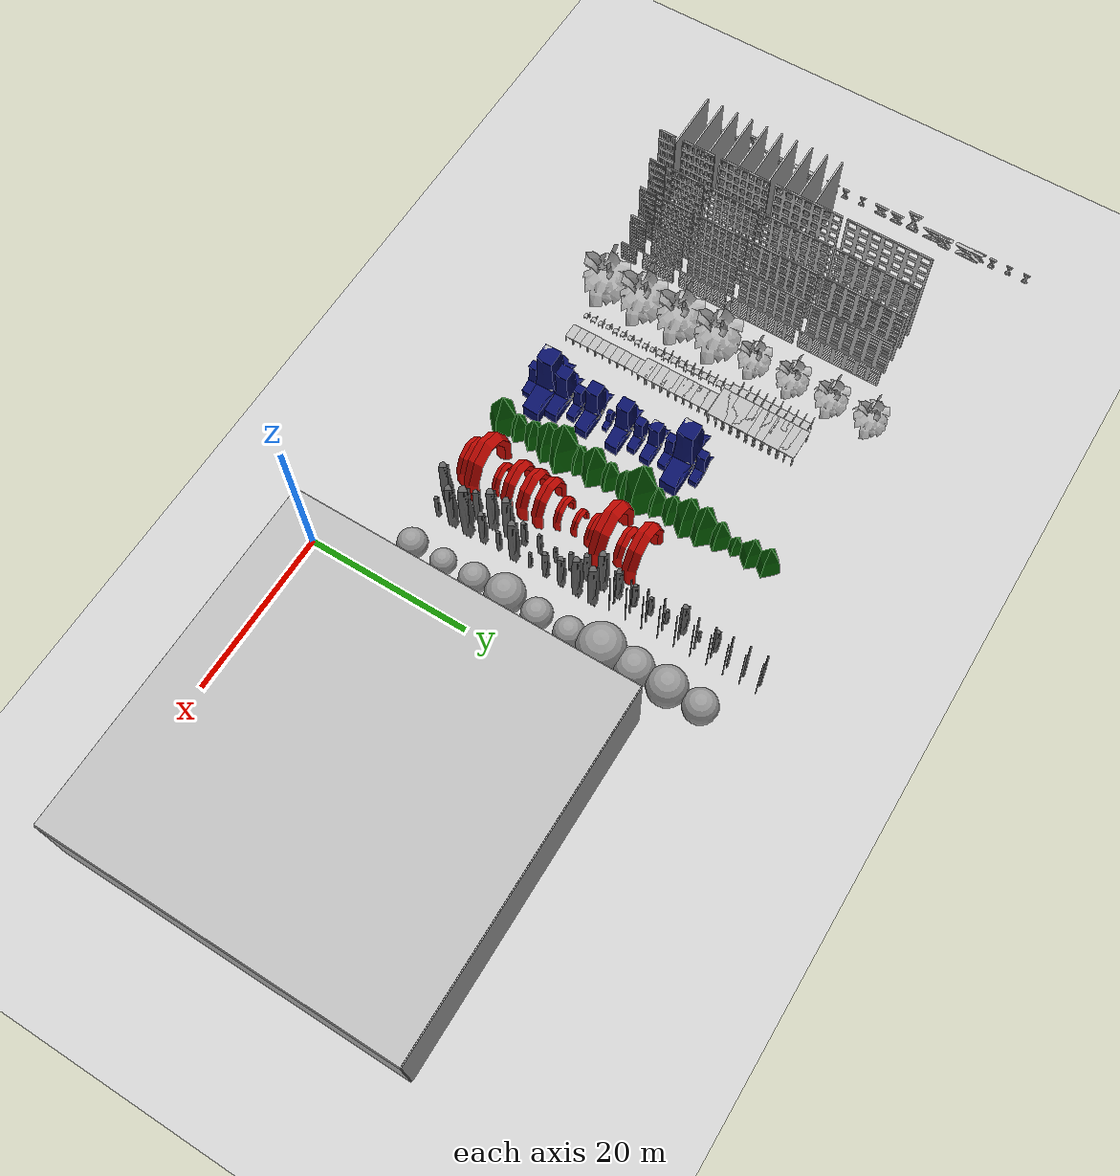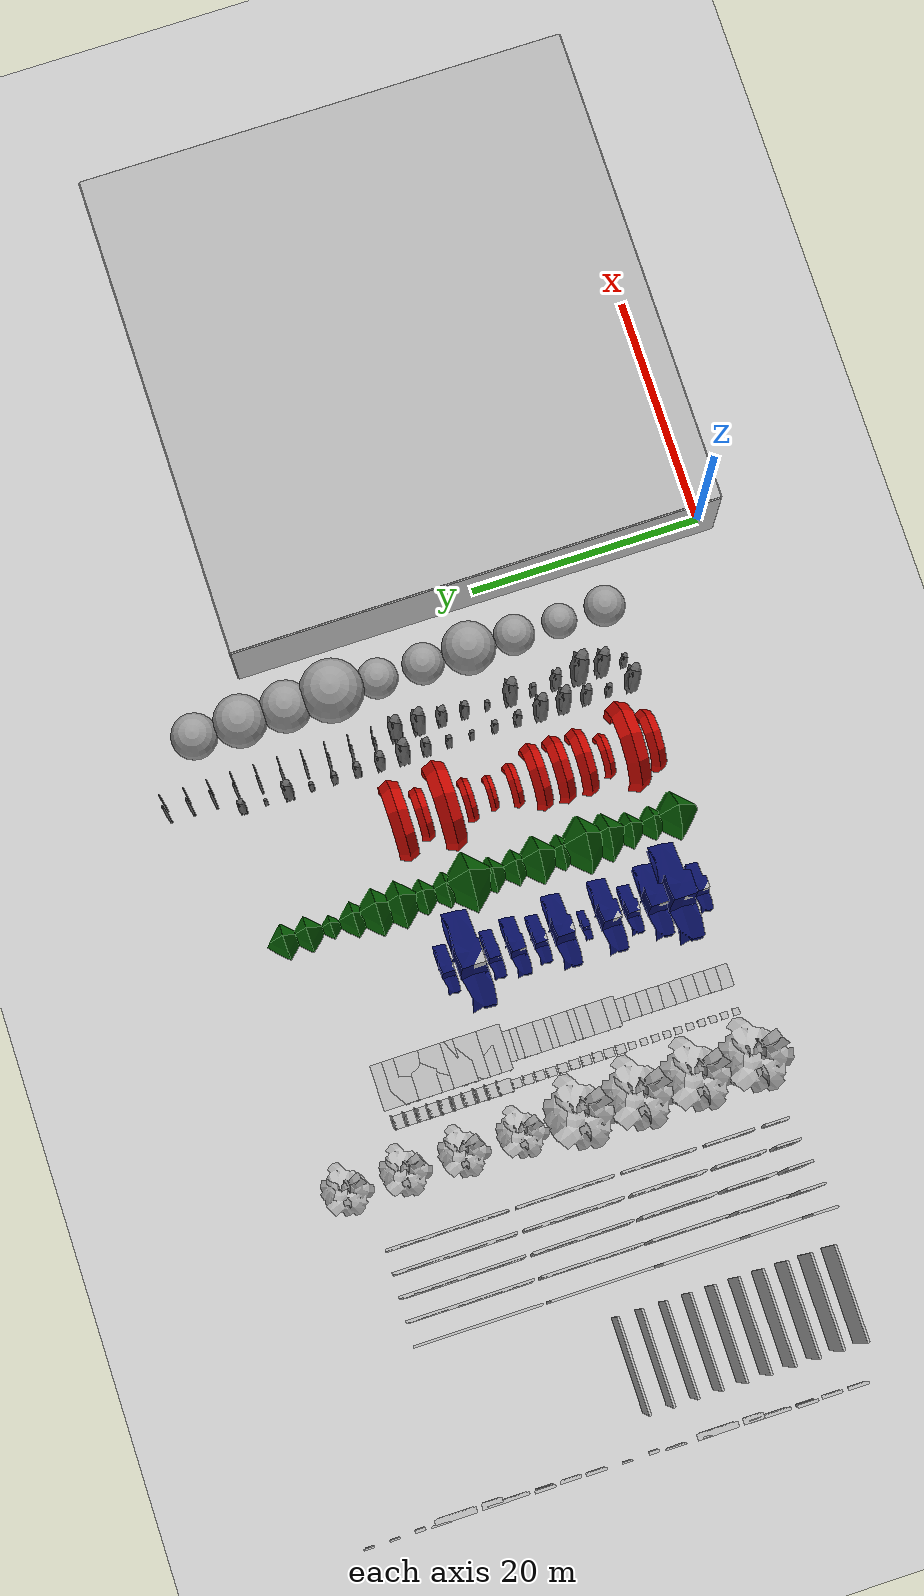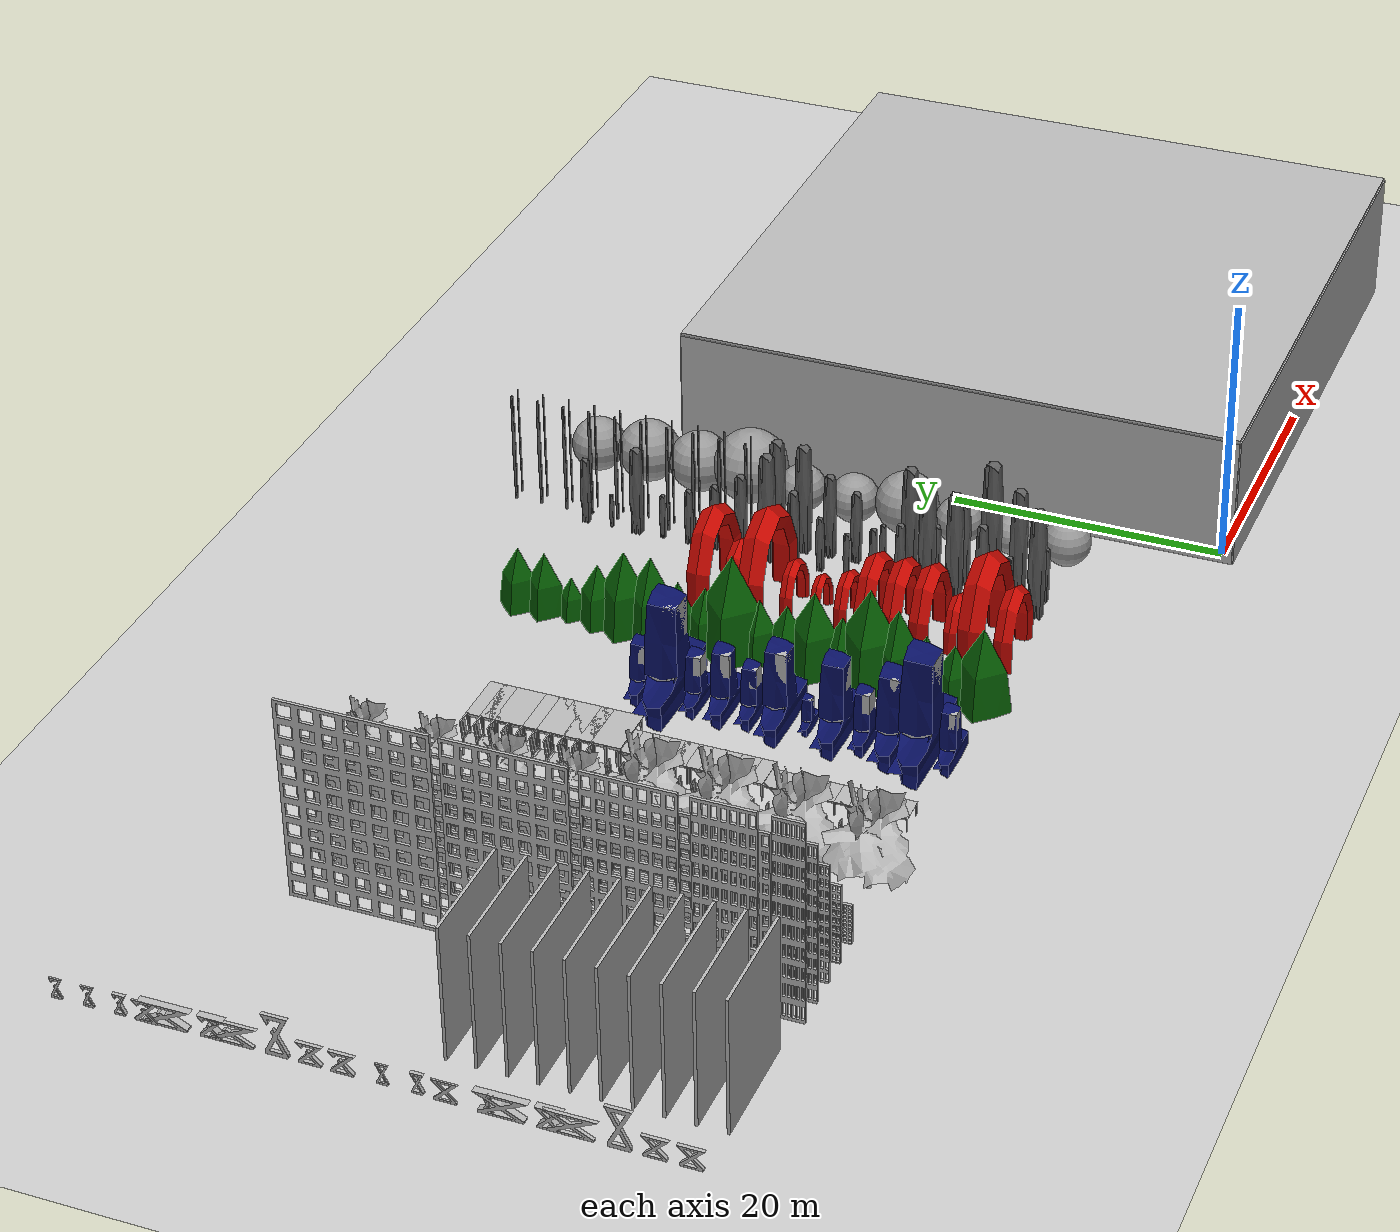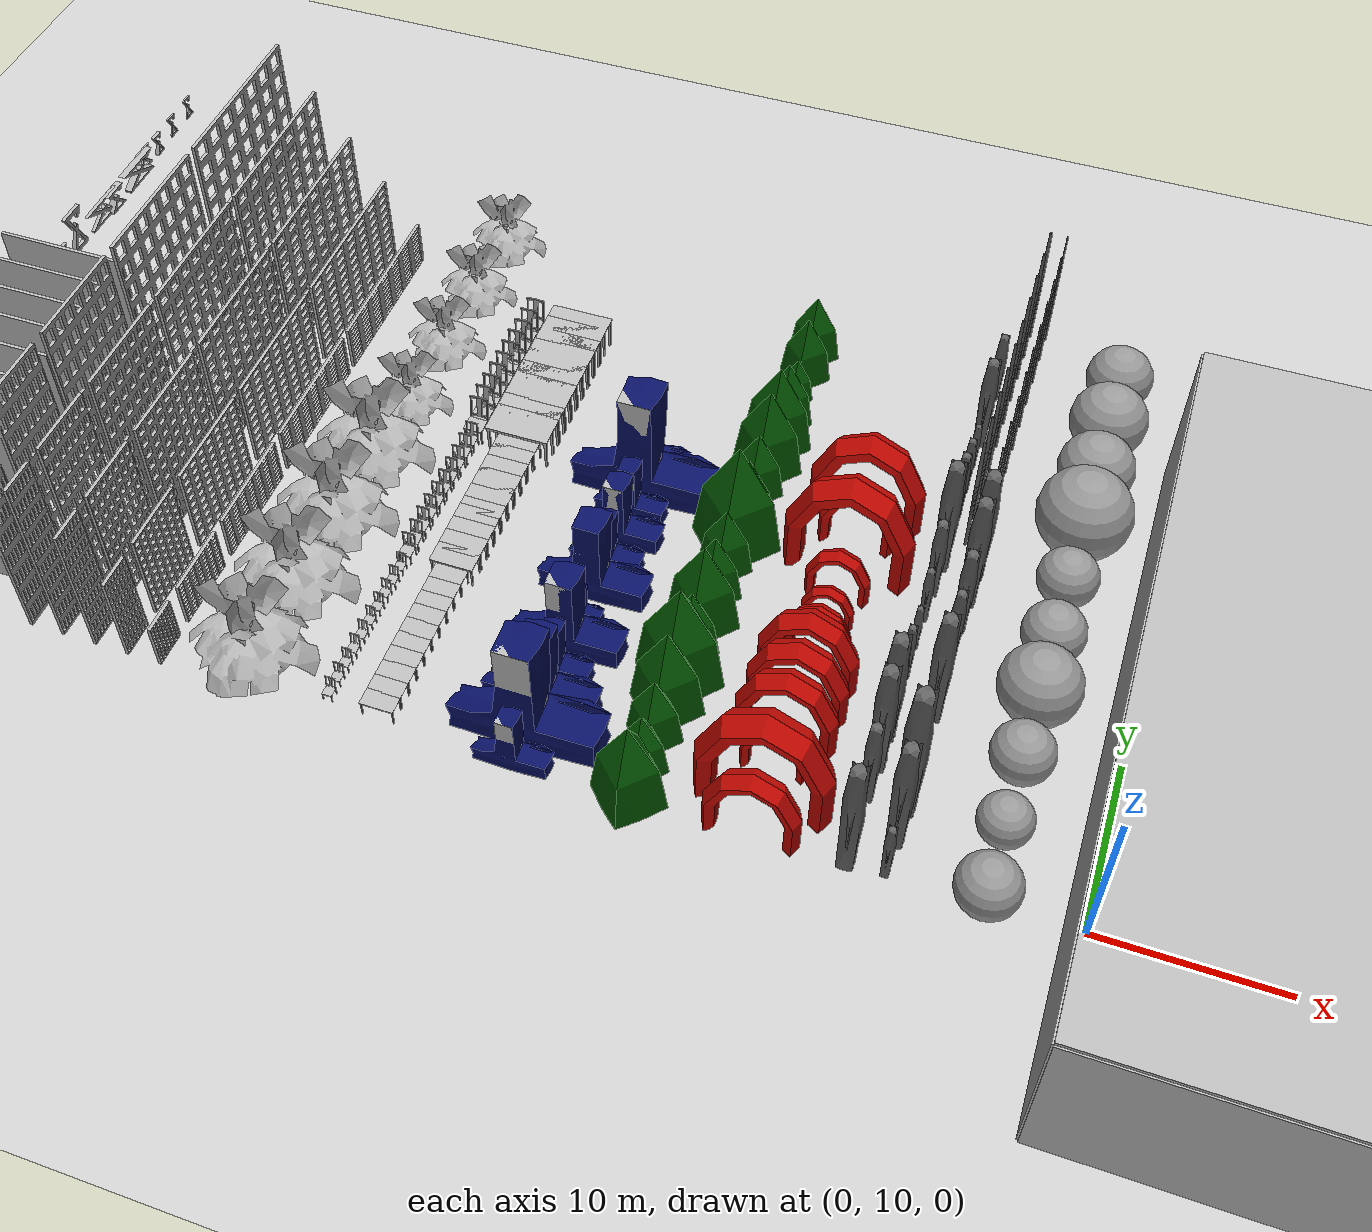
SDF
<sdf version="1.6">
 <world name="default">
  <model name="ground_plane">
   <static>1</static>
   <link name="link">
    <collision name="collision">
     <geometry><plane><normal>0 0 1</normal><size>1000 1000</size></plane></geometry>
     <surface>
      <contact><collide_bitmask>65535</collide_bitmask></contact>
      <friction><ode><mu>100</mu><mu2>50</mu2></ode></friction>
     </surface>
    </collision>
    <visual name="visual">
     <cast_shadows>0</cast_shadows>
     <geometry><plane><normal>0 0 1</normal><size>1000 1000</size></plane></geometry>
     <material>
      <script><uri>file://media/materials/scripts/gazebo.material</uri><name>Gazebo/Grey</name></script>
     </material>
    </visual>
   </link>
  </model>
  <light name="sun" type="directional">
   <pose>0 0 10 0 -0 0</pose>
   <diffuse>0.8 0.8 0.8 1</diffuse>
   <specular>0.2 0.2 0.2 1</specular>
   <attenuation>
    <range>1000</range>
    <constant>0.9</constant>
    <linear>0.01</linear>
    <quadratic>0.001</quadratic>
   </attenuation>
   <direction>-0.5 0.1 -0.9</direction>
  </light>
  <scene><shadows>0</shadows><ambient>0.4 0.4 0.4 1</ambient><background>0.7 0.7 0.7 1</background></scene>
  <plugin name="ros_interface_plugin" filename="librotors_gazebo_ros_interface_plugin.so"/>
  <physics name="default_physics" default="0" type="ode">
   <max_step_size>0.005</max_step_size>
   <real_time_factor>10</real_time_factor>
   <real_time_update_rate>600</real_time_update_rate>
   <ode>
    <solver>
     <type>quick</type>
     <iters>1000</iters>
     <sor>1.3</sor>
     <use_dynamic_moi_rescaling>0</use_dynamic_moi_rescaling>
    </solver>
    <constraints>
     <cfm>0</cfm>
     <erp>0.2</erp>
     <contact_max_correcting_vel>100</contact_max_correcting_vel>
     <contact_surface_layer>0.001</contact_surface_layer>
    </constraints>
   </ode>
  </physics>
  <gravity>0 0 -9.8</gravity>
  <magnetic_field>6e-06 2.3e-05 -4.2e-05</magnetic_field>
  <atmosphere type="adiabatic"/>
  <audio><device>default</device></audio>
  <spherical_coordinates>
   <surface_model>EARTH_WGS84</surface_model>
   <latitude_deg>0</latitude_deg>
   <longitude_deg>0</longitude_deg>
   <elevation>0</elevation>
   <heading_deg>0</heading_deg>
  </spherical_coordinates>
  <model name="wall_top">
   <static>1</static>
   <link name="link">
    <pose>0 0 0.1 0 0 0</pose>
    <collision name="collision"><geometry><box><size>42.0 42.0 0.2</size></box></geometry></collision>
    <visual name="visual">
     <cast_shadows>0</cast_shadows>
     <geometry><box><size>42.0 42.0 0.2</size></box></geometry>
    </visual>
   </link>
   <pose>20.0 20.0 10.0 0 0 0</pose>
  </model>
  <model name="Simple Block_6">
   <pose>-30 22 0 0 -0 0</pose>
   <static>1</static>
   <link name="link">
    <collision name="collision">
     <geometry>
      <mesh><uri>model://Simple Block/meshes/Simple Block.dae</uri><scale>0.75 0.75 0.75</scale></mesh>
     </geometry>
    </collision>
    <visual name="visual">
     <geometry>
      <mesh><uri>model://Simple Block/meshes/Simple Block.dae</uri><scale>0.75 0.75 0.75</scale></mesh>
     </geometry>
    </visual>
   </link>
  </model>
  <model name="Simple Block_0">
   <pose>-30 10 0 0 -0 0</pose>
   <static>1</static>
   <link name="link">
    <collision name="collision">
     <geometry>
      <mesh><uri>model://Simple Block/meshes/Simple Block.dae</uri><scale>0.5 0.5 0.5</scale></mesh>
     </geometry>
    </collision>
    <visual name="visual">
     <geometry>
      <mesh><uri>model://Simple Block/meshes/Simple Block.dae</uri><scale>0.5 0.5 0.5</scale></mesh>
     </geometry>
    </visual>
   </link>
  </model>
  <model name="Simple Block_1">
   <pose>-30 12 0 0 -0 0</pose>
   <static>1</static>
   <link name="link">
    <collision name="collision">
     <geometry><mesh><uri>model://Simple Block/meshes/Simple Block.dae</uri></mesh></geometry>
    </collision>
    <visual name="visual">
     <geometry><mesh><uri>model://Simple Block/meshes/Simple Block.dae</uri></mesh></geometry>
    </visual>
   </link>
  </model>
  <model name="Simple Block_2">
   <pose>-30 14 0 0 -0 0</pose>
   <static>1</static>
   <link name="link">
    <collision name="collision">
     <geometry>
      <mesh><uri>model://Simple Block/meshes/Simple Block.dae</uri><scale>0.75 0.75 0.75</scale></mesh>
     </geometry>
    </collision>
    <visual name="visual">
     <geometry>
      <mesh><uri>model://Simple Block/meshes/Simple Block.dae</uri><scale>0.75 0.75 0.75</scale></mesh>
     </geometry>
    </visual>
   </link>
  </model>
  <model name="Simple Block_3">
   <pose>-30 16 0 0 -0 0</pose>
   <static>1</static>
   <link name="link">
    <collision name="collision">
     <geometry>
      <mesh><uri>model://Simple Block/meshes/Simple Block.dae</uri><scale>0.5 0.5 0.5</scale></mesh>
     </geometry>
    </collision>
    <visual name="visual">
     <geometry>
      <mesh><uri>model://Simple Block/meshes/Simple Block.dae</uri><scale>0.5 0.5 0.5</scale></mesh>
     </geometry>
    </visual>
   </link>
  </model>
  <model name="Simple Block_4">
   <pose>-30 18 0 0 -0 0</pose>
   <static>1</static>
   <link name="link">
    <collision name="collision">
     <geometry>
      <mesh><uri>model://Simple Block/meshes/Simple Block.dae</uri><scale>0.75 0.75 0.75</scale></mesh>
     </geometry>
    </collision>
    <visual name="visual">
     <geometry>
      <mesh><uri>model://Simple Block/meshes/Simple Block.dae</uri><scale>0.75 0.75 0.75</scale></mesh>
     </geometry>
    </visual>
   </link>
  </model>
  <model name="Simple Block_5">
   <pose>-30 20 0 0 -0 0</pose>
   <static>1</static>
   <link name="link">
    <collision name="collision">
     <geometry>
      <mesh><uri>model://Simple Block/meshes/Simple Block.dae</uri><scale>0.3 0.3 0.3</scale></mesh>
     </geometry>
    </collision>
    <visual name="visual">
     <geometry>
      <mesh><uri>model://Simple Block/meshes/Simple Block.dae</uri><scale>0.3 0.3 0.3</scale></mesh>
     </geometry>
    </visual>
   </link>
  </model>
  <model name="Simple Pyramid_11">
   <pose>-23.5 32 0 0 -0 0</pose>
   <static>1</static>
   <link name="link">
    <collision name="collision">
     <geometry>
      <mesh><uri>model://Simple Pyramid/meshes/Simple Pyramid.dae</uri><scale>0.75 0.75 0.75</scale></mesh>
     </geometry>
    </collision>
    <visual name="visual">
     <geometry>
      <mesh><uri>model://Simple Pyramid/meshes/Simple Pyramid.dae</uri><scale>0.75 0.75 0.75</scale></mesh>
     </geometry>
    </visual>
   </link>
  </model>
  <model name="Simple Pyramid_0">
   <pose>-23.5 10 0 0 -0 0</pose>
   <static>1</static>
   <link name="link">
    <collision name="collision">
     <geometry><mesh><uri>model://Simple Pyramid/meshes/Simple Pyramid.dae</uri></mesh></geometry>
    </collision>
    <visual name="visual">
     <geometry><mesh><uri>model://Simple Pyramid/meshes/Simple Pyramid.dae</uri></mesh></geometry>
    </visual>
   </link>
  </model>
  <model name="Simple Pyramid_1">
   <pose>-23.5 12 0 0 -0 0</pose>
   <static>1</static>
   <link name="link">
    <collision name="collision">
     <geometry>
      <mesh><uri>model://Simple Pyramid/meshes/Simple Pyramid.dae</uri><scale>0.7 0.7 0.7</scale></mesh>
     </geometry>
    </collision>
    <visual name="visual">
     <geometry>
      <mesh><uri>model://Simple Pyramid/meshes/Simple Pyramid.dae</uri><scale>0.7 0.7 0.7</scale></mesh>
     </geometry>
    </visual>
   </link>
  </model>
  <model name="Simple Pyramid_2">
   <pose>-23.5 14 0 0 -0 0</pose>
   <static>1</static>
   <link name="link">
    <collision name="collision">
     <geometry>
      <mesh><uri>model://Simple Pyramid/meshes/Simple Pyramid.dae</uri><scale>0.75 0.75 0.75</scale></mesh>
     </geometry>
    </collision>
    <visual name="visual">
     <geometry>
      <mesh><uri>model://Simple Pyramid/meshes/Simple Pyramid.dae</uri><scale>0.75 0.75 0.75</scale></mesh>
     </geometry>
    </visual>
   </link>
  </model>
  <model name="Simple Pyramid_3">
   <pose>-23.5 16 0 0 -0 0</pose>
   <static>1</static>
   <link name="link">
    <collision name="collision">
     <geometry><mesh><uri>model://Simple Pyramid/meshes/Simple Pyramid.dae</uri></mesh></geometry>
    </collision>
    <visual name="visual">
     <geometry><mesh><uri>model://Simple Pyramid/meshes/Simple Pyramid.dae</uri></mesh></geometry>
    </visual>
   </link>
  </model>
  <model name="Simple Pyramid_4">
   <pose>-23.5 18 0 0 -0 0</pose>
   <static>1</static>
   <link name="link">
    <collision name="collision">
     <geometry>
      <mesh><uri>model://Simple Pyramid/meshes/Simple Pyramid.dae</uri><scale>1.2 1.2 1.2</scale></mesh>
     </geometry>
    </collision>
    <visual name="visual">
     <geometry>
      <mesh><uri>model://Simple Pyramid/meshes/Simple Pyramid.dae</uri><scale>1.2 1.2 1.2</scale></mesh>
     </geometry>
    </visual>
   </link>
  </model>
  <model name="Simple Pyramid_5">
   <pose>-23.5 20 0 0 -0 0</pose>
   <static>1</static>
   <link name="link">
    <collision name="collision">
     <geometry>
      <mesh><uri>model://Simple Pyramid/meshes/Simple Pyramid.dae</uri><scale>0.75 0.75 0.75</scale></mesh>
     </geometry>
    </collision>
    <visual name="visual">
     <geometry>
      <mesh><uri>model://Simple Pyramid/meshes/Simple Pyramid.dae</uri><scale>0.75 0.75 0.75</scale></mesh>
     </geometry>
    </visual>
   </link>
  </model>
  <model name="Simple Pyramid_6">
   <pose>-23.5 22 0 0 -0 0</pose>
   <static>1</static>
   <link name="link">
    <collision name="collision">
     <geometry><mesh><uri>model://Simple Pyramid/meshes/Simple Pyramid.dae</uri></mesh></geometry>
    </collision>
    <visual name="visual">
     <geometry><mesh><uri>model://Simple Pyramid/meshes/Simple Pyramid.dae</uri></mesh></geometry>
    </visual>
   </link>
  </model>
  <model name="Simple Pyramid_7">
   <pose>-23.5 24 0 0 -0 0</pose>
   <static>1</static>
   <link name="link">
    <collision name="collision">
     <geometry>
      <mesh><uri>model://Simple Pyramid/meshes/Simple Pyramid.dae</uri><scale>0.75 0.75 0.75</scale></mesh>
     </geometry>
    </collision>
    <visual name="visual">
     <geometry>
      <mesh><uri>model://Simple Pyramid/meshes/Simple Pyramid.dae</uri><scale>0.75 0.75 0.75</scale></mesh>
     </geometry>
    </visual>
   </link>
  </model>
  <model name="Simple Pyramid_8">
   <pose>-23.5 26 0 0 -0 0</pose>
   <static>1</static>
   <link name="link">
    <collision name="collision">
     <geometry>
      <mesh><uri>model://Simple Pyramid/meshes/Simple Pyramid.dae</uri><scale>0.75 0.75 0.75</scale></mesh>
     </geometry>
    </collision>
    <visual name="visual">
     <geometry>
      <mesh><uri>model://Simple Pyramid/meshes/Simple Pyramid.dae</uri><scale>0.75 0.75 0.75</scale></mesh>
     </geometry>
    </visual>
   </link>
  </model>
  <model name="Simple Pyramid_9">
   <pose>-23.5 28 0 0 -0 0</pose>
   <static>1</static>
   <link name="link">
    <collision name="collision">
     <geometry>
      <mesh><uri>model://Simple Pyramid/meshes/Simple Pyramid.dae</uri><scale>1.25 1.25 1.25</scale></mesh>
     </geometry>
    </collision>
    <visual name="visual">
     <geometry>
      <mesh><uri>model://Simple Pyramid/meshes/Simple Pyramid.dae</uri><scale>1.25 1.25 1.25</scale></mesh>
     </geometry>
    </visual>
   </link>
  </model>
  <model name="Simple Pyramid_10">
   <pose>-23.5 30 0 0 -0 0</pose>
   <static>1</static>
   <link name="link">
    <collision name="collision">
     <geometry>
      <mesh><uri>model://Simple Pyramid/meshes/Simple Pyramid.dae</uri><scale>0.75 0.75 0.75</scale></mesh>
     </geometry>
    </collision>
    <visual name="visual">
     <geometry>
      <mesh><uri>model://Simple Pyramid/meshes/Simple Pyramid.dae</uri><scale>0.75 0.75 0.75</scale></mesh>
     </geometry>
    </visual>
   </link>
  </model>
  <model name="Simple U_7">
   <pose>-17 24 0 0 -0 0</pose>
   <static>1</static>
   <link name="link">
    <collision name="collision">
     <geometry><mesh><uri>model://Simple U/meshes/Simple U.dae</uri><scale>0.4 0.4 0.4</scale></mesh></geometry>
    </collision>
    <visual name="visual">
     <geometry><mesh><uri>model://Simple U/meshes/Simple U.dae</uri><scale>0.4 0.4 0.4</scale></mesh></geometry>
    </visual>
   </link>
  </model>
  <model name="Simple U_0">
   <pose>-17 10 0 0 -0 0</pose>
   <static>1</static>
   <link name="link">
    <collision name="collision">
     <geometry><mesh><uri>model://Simple U/meshes/Simple U.dae</uri><scale>0.7 0.7 0.7</scale></mesh></geometry>
    </collision>
    <visual name="visual">
     <geometry><mesh><uri>model://Simple U/meshes/Simple U.dae</uri><scale>0.7 0.7 0.7</scale></mesh></geometry>
    </visual>
   </link>
  </model>
  <model name="Simple U_1">
   <pose>-17 12 0 0 -0 0</pose>
   <static>1</static>
   <link name="link">
    <collision name="collision">
     <geometry><mesh><uri>model://Simple U/meshes/Simple U.dae</uri></mesh></geometry>
    </collision>
    <visual name="visual">
     <geometry><mesh><uri>model://Simple U/meshes/Simple U.dae</uri></mesh></geometry>
    </visual>
   </link>
  </model>
  <model name="Simple U_2">
   <pose>-17 14 0 0 -0 0</pose>
   <static>1</static>
   <link name="link">
    <collision name="collision">
     <geometry><mesh><uri>model://Simple U/meshes/Simple U.dae</uri><scale>0.5 0.5 0.5</scale></mesh></geometry>
    </collision>
    <visual name="visual">
     <geometry><mesh><uri>model://Simple U/meshes/Simple U.dae</uri><scale>0.5 0.5 0.5</scale></mesh></geometry>
    </visual>
   </link>
  </model>
  <model name="Simple U_3">
   <pose>-17 16 0 0 -0 0</pose>
   <static>1</static>
   <link name="link">
    <collision name="collision">
     <geometry><mesh><uri>model://Simple U/meshes/Simple U.dae</uri><scale>0.75 0.75 0.75</scale></mesh></geometry>
    </collision>
    <visual name="visual">
     <geometry><mesh><uri>model://Simple U/meshes/Simple U.dae</uri><scale>0.75 0.75 0.75</scale></mesh></geometry>
    </visual>
   </link>
  </model>
  <model name="Simple U_4">
   <pose>-17 18 0 0 -0 0</pose>
   <static>1</static>
   <link name="link">
    <collision name="collision">
     <geometry><mesh><uri>model://Simple U/meshes/Simple U.dae</uri><scale>0.75 0.75 0.75</scale></mesh></geometry>
    </collision>
    <visual name="visual">
     <geometry><mesh><uri>model://Simple U/meshes/Simple U.dae</uri><scale>0.75 0.75 0.75</scale></mesh></geometry>
    </visual>
   </link>
  </model>
  <model name="Simple U_5">
   <pose>-17 20 0 0 -0 0</pose>
   <static>1</static>
   <link name="link">
    <collision name="collision">
     <geometry><mesh><uri>model://Simple U/meshes/Simple U.dae</uri><scale>0.75 0.75 0.75</scale></mesh></geometry>
    </collision>
    <visual name="visual">
     <geometry><mesh><uri>model://Simple U/meshes/Simple U.dae</uri><scale>0.75 0.75 0.75</scale></mesh></geometry>
    </visual>
   </link>
  </model>
  <model name="Simple U_6">
   <pose>-17 22 0 0 -0 0</pose>
   <static>1</static>
   <link name="link">
    <collision name="collision">
     <geometry><mesh><uri>model://Simple U/meshes/Simple U.dae</uri><scale>0.5 0.5 0.5</scale></mesh></geometry>
    </collision>
    <visual name="visual">
     <geometry><mesh><uri>model://Simple U/meshes/Simple U.dae</uri><scale>0.5 0.5 0.5</scale></mesh></geometry>
    </visual>
   </link>
  </model>
  <model name="Simple Stone_25">
   <pose>-10 24 0 0 -0 0</pose>
   <static>1</static>
   <link name="link">
    <collision name="collision">
     <geometry>
      <mesh><uri>model://Simple Stone/meshes/Simple Stone.dae</uri><scale>0.66 0.66 0.66</scale></mesh>
     </geometry>
    </collision>
    <visual name="visual">
     <geometry>
      <mesh><uri>model://Simple Stone/meshes/Simple Stone.dae</uri><scale>0.66 0.66 0.66</scale></mesh>
     </geometry>
    </visual>
   </link>
  </model>
  <model name="Simple Stone_0">
   <pose>-12 10 0 0 -0 0</pose>
   <static>1</static>
   <link name="link">
    <collision name="collision">
     <geometry><mesh><uri>model://Simple Stone/meshes/Simple Stone.dae</uri></mesh></geometry>
    </collision>
    <visual name="visual">
     <geometry><mesh><uri>model://Simple Stone/meshes/Simple Stone.dae</uri></mesh></geometry>
    </visual>
   </link>
  </model>
  <model name="Simple Stone_1">
   <pose>-12 12 0 0 -0 0</pose>
   <static>1</static>
   <link name="link">
    <collision name="collision">
     <geometry>
      <mesh><uri>model://Simple Stone/meshes/Simple Stone.dae</uri><scale>0.5 0.5 0.5</scale></mesh>
     </geometry>
    </collision>
    <visual name="visual">
     <geometry>
      <mesh><uri>model://Simple Stone/meshes/Simple Stone.dae</uri><scale>0.5 0.5 0.5</scale></mesh>
     </geometry>
    </visual>
   </link>
  </model>
  <model name="Simple Stone_2">
   <pose>-12 14 0 0 -0 0</pose>
   <static>1</static>
   <link name="link">
    <collision name="collision">
     <geometry>
      <mesh><uri>model://Simple Stone/meshes/Simple Stone.dae</uri><scale>0.75 0.75 0.75</scale></mesh>
     </geometry>
    </collision>
    <visual name="visual">
     <geometry>
      <mesh><uri>model://Simple Stone/meshes/Simple Stone.dae</uri><scale>0.75 0.75 0.75</scale></mesh>
     </geometry>
    </visual>
   </link>
  </model>
  <model name="Simple Stone_3">
   <pose>-12 16 0 0 -0 0</pose>
   <static>1</static>
   <link name="link">
    <collision name="collision">
     <geometry><mesh><uri>model://Simple Stone/meshes/Simple Stone.dae</uri></mesh></geometry>
    </collision>
    <visual name="visual">
     <geometry><mesh><uri>model://Simple Stone/meshes/Simple Stone.dae</uri></mesh></geometry>
    </visual>
   </link>
  </model>
  <model name="Simple Stone_4">
   <pose>-12 18 0 0 -0 0</pose>
   <static>1</static>
   <link name="link">
    <collision name="collision">
     <geometry><mesh><uri>model://Simple Stone/meshes/Simple Stone.dae</uri></mesh></geometry>
    </collision>
    <visual name="visual">
     <geometry><mesh><uri>model://Simple Stone/meshes/Simple Stone.dae</uri></mesh></geometry>
    </visual>
   </link>
  </model>
  <model name="Simple Stone_5">
   <pose>-12 20 0 0 -0 0</pose>
   <static>1</static>
   <link name="link">
    <collision name="collision">
     <geometry>
      <mesh><uri>model://Simple Stone/meshes/Simple Stone.dae</uri><scale>0.6 0.6 0.6</scale></mesh>
     </geometry>
    </collision>
    <visual name="visual">
     <geometry>
      <mesh><uri>model://Simple Stone/meshes/Simple Stone.dae</uri><scale>0.6 0.6 0.6</scale></mesh>
     </geometry>
    </visual>
   </link>
  </model>
  <model name="Simple Stone_6">
   <pose>-12 22 0 0 -0 0</pose>
   <static>1</static>
   <link name="link">
    <collision name="collision">
     <geometry>
      <mesh><uri>model://Simple Stone/meshes/Simple Stone.dae</uri><scale>0.5 0.5 0.5</scale></mesh>
     </geometry>
    </collision>
    <visual name="visual">
     <geometry>
      <mesh><uri>model://Simple Stone/meshes/Simple Stone.dae</uri><scale>0.5 0.5 0.5</scale></mesh>
     </geometry>
    </visual>
   </link>
  </model>
  <model name="Simple Stone_7">
   <pose>-12 24 0 0 -0 0</pose>
   <static>1</static>
   <link name="link">
    <collision name="collision">
     <geometry>
      <mesh><uri>model://Simple Stone/meshes/Simple Stone.dae</uri><scale>0.4 0.4 0.4</scale></mesh>
     </geometry>
    </collision>
    <visual name="visual">
     <geometry>
      <mesh><uri>model://Simple Stone/meshes/Simple Stone.dae</uri><scale>0.4 0.4 0.4</scale></mesh>
     </geometry>
    </visual>
   </link>
  </model>
  <model name="Simple Stone_8">
   <pose>-12 26 0 0 -0 0</pose>
   <static>1</static>
   <link name="link">
    <collision name="collision">
     <geometry>
      <mesh><uri>model://Simple Stone/meshes/Simple Stone.dae</uri><scale>0.5 0.5 0.5</scale></mesh>
     </geometry>
    </collision>
    <visual name="visual">
     <geometry>
      <mesh><uri>model://Simple Stone/meshes/Simple Stone.dae</uri><scale>0.5 0.5 0.5</scale></mesh>
     </geometry>
    </visual>
   </link>
  </model>
  <model name="Simple Stone_9">
   <pose>-12 28 0 0 -0 0</pose>
   <static>1</static>
   <link name="link">
    <collision name="collision">
     <geometry>
      <mesh><uri>model://Simple Stone/meshes/Simple Stone.dae</uri><scale>0.7 0.7 0.7</scale></mesh>
     </geometry>
    </collision>
    <visual name="visual">
     <geometry>
      <mesh><uri>model://Simple Stone/meshes/Simple Stone.dae</uri><scale>0.7 0.7 0.7</scale></mesh>
     </geometry>
    </visual>
   </link>
  </model>
  <model name="Simple Stone_10">
   <pose>-12 30 0 0 -0 0</pose>
   <static>1</static>
   <link name="link">
    <collision name="collision">
     <geometry><mesh><uri>model://Simple Stone/meshes/Simple Stone.dae</uri></mesh></geometry>
    </collision>
    <visual name="visual">
     <geometry><mesh><uri>model://Simple Stone/meshes/Simple Stone.dae</uri></mesh></geometry>
    </visual>
   </link>
  </model>
  <model name="Simple Stone_11">
   <pose>-12 32 0 0 -0 0</pose>
   <static>1</static>
   <link name="link">
    <collision name="collision">
     <geometry>
      <mesh><uri>model://Simple Stone/meshes/Simple Stone.dae</uri><scale>0.75 0.75 0.75</scale></mesh>
     </geometry>
    </collision>
    <visual name="visual">
     <geometry>
      <mesh><uri>model://Simple Stone/meshes/Simple Stone.dae</uri><scale>0.75 0.75 0.75</scale></mesh>
     </geometry>
    </visual>
   </link>
  </model>
  <model name="Simple Stone_12">
   <pose>-12 34 0 0 -0 0</pose>
   <static>1</static>
   <link name="link">
    <collision name="collision">
     <geometry>
      <mesh><uri>model://Simple Stone/meshes/Simple Stone.dae</uri><scale>0.6 0.6 0.6</scale></mesh>
     </geometry>
    </collision>
    <visual name="visual">
     <geometry>
      <mesh><uri>model://Simple Stone/meshes/Simple Stone.dae</uri><scale>0.6 0.6 0.6</scale></mesh>
     </geometry>
    </visual>
   </link>
  </model>
  <model name="Simple Stone_13">
   <pose>-12 36 0 0 -0 0</pose>
   <static>1</static>
   <link name="link">
    <collision name="collision">
     <geometry>
      <mesh><uri>model://Simple Stone/meshes/Simple Stone.dae</uri><scale>0.5 0.5 0.5</scale></mesh>
     </geometry>
    </collision>
    <visual name="visual">
     <geometry>
      <mesh><uri>model://Simple Stone/meshes/Simple Stone.dae</uri><scale>0.5 0.5 0.5</scale></mesh>
     </geometry>
    </visual>
   </link>
  </model>
  <model name="Simple Stone_14">
   <pose>-12 38 0 0 -0 0</pose>
   <static>1</static>
   <link name="link">
    <collision name="collision">
     <geometry>
      <mesh><uri>model://Simple Stone/meshes/Simple Stone.dae</uri><scale>0.4 0.4 0.4</scale></mesh>
     </geometry>
    </collision>
    <visual name="visual">
     <geometry>
      <mesh><uri>model://Simple Stone/meshes/Simple Stone.dae</uri><scale>0.4 0.4 0.4</scale></mesh>
     </geometry>
    </visual>
   </link>
  </model>
  <model name="Simple Stone_15">
   <pose>-12 40 0 0 -0 0</pose>
   <static>1</static>
   <link name="link">
    <collision name="collision">
     <geometry>
      <mesh><uri>model://Simple Stone/meshes/Simple Stone.dae</uri><scale>0.8 0.8 0.8</scale></mesh>
     </geometry>
    </collision>
    <visual name="visual">
     <geometry>
      <mesh><uri>model://Simple Stone/meshes/Simple Stone.dae</uri><scale>0.8 0.8 0.8</scale></mesh>
     </geometry>
    </visual>
   </link>
  </model>
  <model name="Simple Stone_16">
   <pose>-12 42 0 0 -0 0</pose>
   <static>1</static>
   <link name="link">
    <collision name="collision">
     <geometry>
      <mesh><uri>model://Simple Stone/meshes/Simple Stone.dae</uri><scale>0.3 0.3 0.3</scale></mesh>
     </geometry>
    </collision>
    <visual name="visual">
     <geometry>
      <mesh><uri>model://Simple Stone/meshes/Simple Stone.dae</uri><scale>0.3 0.3 0.3</scale></mesh>
     </geometry>
    </visual>
   </link>
  </model>
  <model name="Simple Stone_17">
   <pose>-12 44 0 0 -0 0</pose>
   <static>1</static>
   <link name="link">
    <collision name="collision">
     <geometry>
      <mesh><uri>model://Simple Stone/meshes/Simple Stone.dae</uri><scale>0.6 0.6 0.6</scale></mesh>
     </geometry>
    </collision>
    <visual name="visual">
     <geometry>
      <mesh><uri>model://Simple Stone/meshes/Simple Stone.dae</uri><scale>0.6 0.6 0.6</scale></mesh>
     </geometry>
    </visual>
   </link>
  </model>
  <model name="Simple Stone_18">
   <pose>-10 10 0 0 -0 0</pose>
   <static>1</static>
   <link name="link">
    <collision name="collision">
     <geometry>
      <mesh><uri>model://Simple Stone/meshes/Simple Stone.dae</uri><scale>0.5 0.5 0.5</scale></mesh>
     </geometry>
    </collision>
    <visual name="visual">
     <geometry>
      <mesh><uri>model://Simple Stone/meshes/Simple Stone.dae</uri><scale>0.5 0.5 0.5</scale></mesh>
     </geometry>
    </visual>
   </link>
  </model>
  <model name="Simple Stone_19">
   <pose>-10 12 0 0 -0 0</pose>
   <static>1</static>
   <link name="link">
    <collision name="collision">
     <geometry><mesh><uri>model://Simple Stone/meshes/Simple Stone.dae</uri></mesh></geometry>
    </collision>
    <visual name="visual">
     <geometry><mesh><uri>model://Simple Stone/meshes/Simple Stone.dae</uri></mesh></geometry>
    </visual>
   </link>
  </model>
  <model name="Simple Stone_20">
   <pose>-10 14 0 0 -0 0</pose>
   <static>1</static>
   <link name="link">
    <collision name="collision">
     <geometry>
      <mesh><uri>model://Simple Stone/meshes/Simple Stone.dae</uri><scale>1.2 1.2 1.2</scale></mesh>
     </geometry>
    </collision>
    <visual name="visual">
     <geometry>
      <mesh><uri>model://Simple Stone/meshes/Simple Stone.dae</uri><scale>1.2 1.2 1.2</scale></mesh>
     </geometry>
    </visual>
   </link>
  </model>
  <model name="Simple Stone_21">
   <pose>-10 16 0 0 -0 0</pose>
   <static>1</static>
   <link name="link">
    <collision name="collision">
     <geometry>
      <mesh><uri>model://Simple Stone/meshes/Simple Stone.dae</uri><scale>0.77 0.77 0.77</scale></mesh>
     </geometry>
    </collision>
    <visual name="visual">
     <geometry>
      <mesh><uri>model://Simple Stone/meshes/Simple Stone.dae</uri><scale>0.77 0.77 0.77</scale></mesh>
     </geometry>
    </visual>
   </link>
  </model>
  <model name="Simple Stone_22">
   <pose>-10 18 0 0 -0 0</pose>
   <static>1</static>
   <link name="link">
    <collision name="collision">
     <geometry>
      <mesh><uri>model://Simple Stone/meshes/Simple Stone.dae</uri><scale>0.5 0.5 0.5</scale></mesh>
     </geometry>
    </collision>
    <visual name="visual">
     <geometry>
      <mesh><uri>model://Simple Stone/meshes/Simple Stone.dae</uri><scale>0.5 0.5 0.5</scale></mesh>
     </geometry>
    </visual>
   </link>
  </model>
  <model name="Simple Stone_23">
   <pose>-10 20 0 0 -0 0</pose>
   <static>1</static>
   <link name="link">
    <collision name="collision">
     <geometry><mesh><uri>model://Simple Stone/meshes/Simple Stone.dae</uri></mesh></geometry>
    </collision>
    <visual name="visual">
     <geometry><mesh><uri>model://Simple Stone/meshes/Simple Stone.dae</uri></mesh></geometry>
    </visual>
   </link>
  </model>
  <model name="Simple Stone_24">
   <pose>-10 22 0 0 -0 0</pose>
   <static>1</static>
   <link name="link">
    <collision name="collision">
     <geometry>
      <mesh><uri>model://Simple Stone/meshes/Simple Stone.dae</uri><scale>0.4 0.4 0.4</scale></mesh>
     </geometry>
    </collision>
    <visual name="visual">
     <geometry>
      <mesh><uri>model://Simple Stone/meshes/Simple Stone.dae</uri><scale>0.4 0.4 0.4</scale></mesh>
     </geometry>
    </visual>
   </link>
  </model>
  <model name="Simple Block_11">
   <pose>-30 32 0 0 -0 0</pose>
   <static>1</static>
   <link name="link">
    <collision name="collision">
     <geometry>
      <mesh><uri>model://Simple Block/meshes/Simple Block.dae</uri><scale>0.5 0.5 0.5</scale></mesh>
     </geometry>
    </collision>
    <visual name="visual">
     <geometry>
      <mesh><uri>model://Simple Block/meshes/Simple Block.dae</uri><scale>0.5 0.5 0.5</scale></mesh>
     </geometry>
    </visual>
   </link>
  </model>
  <model name="Simple Pyramid_17">
   <pose>-23.5 44 0 0 -0 0</pose>
   <static>1</static>
   <link name="link">
    <collision name="collision">
     <geometry>
      <mesh><uri>model://Simple Pyramid/meshes/Simple Pyramid.dae</uri><scale>0.75 0.75 0.75</scale></mesh>
     </geometry>
    </collision>
    <visual name="visual">
     <geometry>
      <mesh><uri>model://Simple Pyramid/meshes/Simple Pyramid.dae</uri><scale>0.75 0.75 0.75</scale></mesh>
     </geometry>
    </visual>
   </link>
  </model>
  <model name="Simple U_11">
   <pose>-17 32 0 0 -0 0</pose>
   <static>1</static>
   <link name="link">
    <collision name="collision">
     <geometry><mesh><uri>model://Simple U/meshes/Simple U.dae</uri><scale>0.9 0.9 0.9</scale></mesh></geometry>
    </collision>
    <visual name="visual">
     <geometry><mesh><uri>model://Simple U/meshes/Simple U.dae</uri><scale>0.9 0.9 0.9</scale></mesh></geometry>
    </visual>
   </link>
  </model>
  <model name="Simple U_8">
   <pose>-17 26 0 0 -0 0</pose>
   <static>1</static>
   <link name="link">
    <collision name="collision">
     <geometry><mesh><uri>model://Simple U/meshes/Simple U.dae</uri><scale>0.5 0.5 0.5</scale></mesh></geometry>
    </collision>
    <visual name="visual">
     <geometry><mesh><uri>model://Simple U/meshes/Simple U.dae</uri><scale>0.5 0.5 0.5</scale></mesh></geometry>
    </visual>
   </link>
  </model>
  <model name="Simple U_9">
   <pose>-17 28 0 0 -0 0</pose>
   <static>1</static>
   <link name="link">
    <collision name="collision">
     <geometry><mesh><uri>model://Simple U/meshes/Simple U.dae</uri></mesh></geometry>
    </collision>
    <visual name="visual">
     <geometry><mesh><uri>model://Simple U/meshes/Simple U.dae</uri></mesh></geometry>
    </visual>
   </link>
  </model>
  <model name="Simple Block_7">
   <pose>-30 24 0 0 -0 0</pose>
   <static>1</static>
   <link name="link">
    <collision name="collision">
     <geometry>
      <mesh><uri>model://Simple Block/meshes/Simple Block.dae</uri><scale>0.5 0.5 0.5</scale></mesh>
     </geometry>
    </collision>
    <visual name="visual">
     <geometry>
      <mesh><uri>model://Simple Block/meshes/Simple Block.dae</uri><scale>0.5 0.5 0.5</scale></mesh>
     </geometry>
    </visual>
   </link>
  </model>
  <model name="Simple Block_8">
   <pose>-30 26 0 0 -0 0</pose>
   <static>1</static>
   <link name="link">
    <collision name="collision">
     <geometry>
      <mesh><uri>model://Simple Block/meshes/Simple Block.dae</uri><scale>0.6 0.6 0.6</scale></mesh>
     </geometry>
    </collision>
    <visual name="visual">
     <geometry>
      <mesh><uri>model://Simple Block/meshes/Simple Block.dae</uri><scale>0.6 0.6 0.6</scale></mesh>
     </geometry>
    </visual>
   </link>
  </model>
  <model name="Simple Block_9">
   <pose>-30 28 0 0 -0 0</pose>
   <static>1</static>
   <link name="link">
    <collision name="collision">
     <geometry>
      <mesh><uri>model://Simple Block/meshes/Simple Block.dae</uri><scale>0.5 0.5 0.5</scale></mesh>
     </geometry>
    </collision>
    <visual name="visual">
     <geometry>
      <mesh><uri>model://Simple Block/meshes/Simple Block.dae</uri><scale>0.5 0.5 0.5</scale></mesh>
     </geometry>
    </visual>
   </link>
  </model>
  <model name="Simple Pyramid_12">
   <pose>-23.5 34 0 0 -0 0</pose>
   <static>1</static>
   <link name="link">
    <collision name="collision">
     <geometry><mesh><uri>model://Simple Pyramid/meshes/Simple Pyramid.dae</uri></mesh></geometry>
    </collision>
    <visual name="visual">
     <geometry><mesh><uri>model://Simple Pyramid/meshes/Simple Pyramid.dae</uri></mesh></geometry>
    </visual>
   </link>
  </model>
  <model name="Simple Pyramid_13">
   <pose>-23.5 36 0 0 -0 0</pose>
   <static>1</static>
   <link name="link">
    <collision name="collision">
     <geometry><mesh><uri>model://Simple Pyramid/meshes/Simple Pyramid.dae</uri></mesh></geometry>
    </collision>
    <visual name="visual">
     <geometry><mesh><uri>model://Simple Pyramid/meshes/Simple Pyramid.dae</uri></mesh></geometry>
    </visual>
   </link>
  </model>
  <model name="Simple Pyramid_14">
   <pose>-23.5 38 0 0 -0 0</pose>
   <static>1</static>
   <link name="link">
    <collision name="collision">
     <geometry>
      <mesh><uri>model://Simple Pyramid/meshes/Simple Pyramid.dae</uri><scale>0.75 0.75 0.75</scale></mesh>
     </geometry>
    </collision>
    <visual name="visual">
     <geometry>
      <mesh><uri>model://Simple Pyramid/meshes/Simple Pyramid.dae</uri><scale>0.75 0.75 0.75</scale></mesh>
     </geometry>
    </visual>
   </link>
  </model>
  <model name="Simple Pyramid_15">
   <pose>-23.5 40 0 0 -0 0</pose>
   <static>1</static>
   <link name="link">
    <collision name="collision">
     <geometry>
      <mesh><uri>model://Simple Pyramid/meshes/Simple Pyramid.dae</uri><scale>0.5 0.5 0.5</scale></mesh>
     </geometry>
    </collision>
    <visual name="visual">
     <geometry>
      <mesh><uri>model://Simple Pyramid/meshes/Simple Pyramid.dae</uri><scale>0.5 0.5 0.5</scale></mesh>
     </geometry>
    </visual>
   </link>
  </model>
  <model name="Simple Stone_28">
   <pose>-10 30 0 0 -0 0</pose>
   <static>1</static>
   <link name="link">
    <collision name="collision">
     <geometry><mesh><uri>model://Simple Stone/meshes/Simple Stone.dae</uri></mesh></geometry>
    </collision>
    <visual name="visual">
     <geometry><mesh><uri>model://Simple Stone/meshes/Simple Stone.dae</uri></mesh></geometry>
    </visual>
   </link>
  </model>
  <model name="Simple Stone_29">
   <pose>-10 32 0 0 -0 0</pose>
   <static>1</static>
   <link name="link">
    <collision name="collision">
     <geometry>
      <mesh><uri>model://Simple Stone/meshes/Simple Stone.dae</uri><scale>0.1 0.1 1.0</scale></mesh>
     </geometry>
    </collision>
    <visual name="visual">
     <geometry>
      <mesh><uri>model://Simple Stone/meshes/Simple Stone.dae</uri><scale>0.1 0.1 1.0</scale></mesh>
     </geometry>
    </visual>
   </link>
  </model>
  <model name="Simple Stone_30">
   <pose>-10 34 0 0 -0 0</pose>
   <static>1</static>
   <link name="link">
    <collision name="collision">
     <geometry>
      <mesh><uri>model://Simple Stone/meshes/Simple Stone.dae</uri><scale>0.1 0.1 1.0</scale></mesh>
     </geometry>
    </collision>
    <visual name="visual">
     <geometry>
      <mesh><uri>model://Simple Stone/meshes/Simple Stone.dae</uri><scale>0.1 0.1 1.0</scale></mesh>
     </geometry>
    </visual>
   </link>
  </model>
  <model name="Simple Stone_31">
   <pose>-10 36 0 0 -0 0</pose>
   <static>1</static>
   <link name="link">
    <collision name="collision">
     <geometry>
      <mesh><uri>model://Simple Stone/meshes/Simple Stone.dae</uri><scale>0.1 0.1 1.0</scale></mesh>
     </geometry>
    </collision>
    <visual name="visual">
     <geometry>
      <mesh><uri>model://Simple Stone/meshes/Simple Stone.dae</uri><scale>0.1 0.1 1.0</scale></mesh>
     </geometry>
    </visual>
   </link>
  </model>
  <model name="Simple Stone_32">
   <pose>-10 38 0 0 -0 0</pose>
   <static>1</static>
   <link name="link">
    <collision name="collision">
     <geometry>
      <mesh><uri>model://Simple Stone/meshes/Simple Stone.dae</uri><scale>0.1 0.1 1.0</scale></mesh>
     </geometry>
    </collision>
    <visual name="visual">
     <geometry>
      <mesh><uri>model://Simple Stone/meshes/Simple Stone.dae</uri><scale>0.1 0.1 1.0</scale></mesh>
     </geometry>
    </visual>
   </link>
  </model>
  <model name="Simple Stone_33">
   <pose>-10 40 0 0 -0 0</pose>
   <static>1</static>
   <link name="link">
    <collision name="collision">
     <geometry>
      <mesh><uri>model://Simple Stone/meshes/Simple Stone.dae</uri><scale>0.1 0.1 1.0</scale></mesh>
     </geometry>
    </collision>
    <visual name="visual">
     <geometry>
      <mesh><uri>model://Simple Stone/meshes/Simple Stone.dae</uri><scale>0.1 0.1 1.0</scale></mesh>
     </geometry>
    </visual>
   </link>
  </model>
  <model name="Simple Stone_34">
   <pose>-11 32 0 0 -0 0</pose>
   <static>1</static>
   <link name="link">
    <collision name="collision">
     <geometry>
      <mesh><uri>model://Simple Stone/meshes/Simple Stone.dae</uri><scale>0.2 0.2 1.0</scale></mesh>
     </geometry>
    </collision>
    <visual name="visual">
     <geometry>
      <mesh><uri>model://Simple Stone/meshes/Simple Stone.dae</uri><scale>0.2 0.2 1.0</scale></mesh>
     </geometry>
    </visual>
   </link>
  </model>
  <model name="Simple Stone_35">
   <pose>-11 34 0 0 -0 0</pose>
   <static>1</static>
   <link name="link">
    <collision name="collision">
     <geometry>
      <mesh><uri>model://Simple Stone/meshes/Simple Stone.dae</uri><scale>0.2 0.2 1.0</scale></mesh>
     </geometry>
    </collision>
    <visual name="visual">
     <geometry>
      <mesh><uri>model://Simple Stone/meshes/Simple Stone.dae</uri><scale>0.2 0.2 1.0</scale></mesh>
     </geometry>
    </visual>
   </link>
  </model>
  <model name="Simple Stone_36">
   <pose>-11 36 0 0 -0 0</pose>
   <static>1</static>
   <link name="link">
    <collision name="collision">
     <geometry>
      <mesh><uri>model://Simple Stone/meshes/Simple Stone.dae</uri><scale>0.2 0.2 1.0</scale></mesh>
     </geometry>
    </collision>
    <visual name="visual">
     <geometry>
      <mesh><uri>model://Simple Stone/meshes/Simple Stone.dae</uri><scale>0.2 0.2 1.0</scale></mesh>
     </geometry>
    </visual>
   </link>
  </model>
  <model name="Simple Stone_37">
   <pose>-11 38 0 0 -0 0</pose>
   <static>1</static>
   <link name="link">
    <collision name="collision">
     <geometry>
      <mesh><uri>model://Simple Stone/meshes/Simple Stone.dae</uri><scale>0.2 0.2 1.0</scale></mesh>
     </geometry>
    </collision>
    <visual name="visual">
     <geometry>
      <mesh><uri>model://Simple Stone/meshes/Simple Stone.dae</uri><scale>0.2 0.2 1.0</scale></mesh>
     </geometry>
    </visual>
   </link>
  </model>
  <model name="Simple Stone_38">
   <pose>-11 40 0 0 -0 0</pose>
   <static>1</static>
   <link name="link">
    <collision name="collision">
     <geometry>
      <mesh><uri>model://Simple Stone/meshes/Simple Stone.dae</uri><scale>0.2 0.2 1.0</scale></mesh>
     </geometry>
    </collision>
    <visual name="visual">
     <geometry>
      <mesh><uri>model://Simple Stone/meshes/Simple Stone.dae</uri><scale>0.2 0.2 1.0</scale></mesh>
     </geometry>
    </visual>
   </link>
  </model>
  <model name="Simple Stone_39">
   <pose>-10 42 0 0 -0 0</pose>
   <static>1</static>
   <link name="link">
    <collision name="collision">
     <geometry>
      <mesh><uri>model://Simple Stone/meshes/Simple Stone.dae</uri><scale>0.1 0.1 1.0</scale></mesh>
     </geometry>
    </collision>
    <visual name="visual">
     <geometry>
      <mesh><uri>model://Simple Stone/meshes/Simple Stone.dae</uri><scale>0.1 0.1 1.0</scale></mesh>
     </geometry>
    </visual>
   </link>
  </model>
  <model name="Simple Stone_40">
   <pose>-10 44 0 0 -0 0</pose>
   <static>1</static>
   <link name="link">
    <collision name="collision">
     <geometry>
      <mesh><uri>model://Simple Stone/meshes/Simple Stone.dae</uri><scale>0.1 0.1 1.0</scale></mesh>
     </geometry>
    </collision>
    <visual name="visual">
     <geometry>
      <mesh><uri>model://Simple Stone/meshes/Simple Stone.dae</uri><scale>0.1 0.1 1.0</scale></mesh>
     </geometry>
    </visual>
   </link>
  </model>
  <model name="Simple Stone_41">
   <pose>-10 46 0 0 -0 0</pose>
   <static>1</static>
   <link name="link">
    <collision name="collision">
     <geometry>
      <mesh><uri>model://Simple Stone/meshes/Simple Stone.dae</uri><scale>0.1 0.1 1.0</scale></mesh>
     </geometry>
    </collision>
    <visual name="visual">
     <geometry>
      <mesh><uri>model://Simple Stone/meshes/Simple Stone.dae</uri><scale>0.1 0.1 1.0</scale></mesh>
     </geometry>
    </visual>
   </link>
  </model>
  <model name="Simple Stone_42">
   <pose>-10 48 0 0 -0 0</pose>
   <static>1</static>
   <link name="link">
    <collision name="collision">
     <geometry>
      <mesh><uri>model://Simple Stone/meshes/Simple Stone.dae</uri><scale>0.1 0.1 1.0</scale></mesh>
     </geometry>
    </collision>
    <visual name="visual">
     <geometry>
      <mesh><uri>model://Simple Stone/meshes/Simple Stone.dae</uri><scale>0.1 0.1 1.0</scale></mesh>
     </geometry>
    </visual>
   </link>
  </model>
  <model name="Simple Stone_43">
   <pose>-10 50 0 0 -0 0</pose>
   <static>1</static>
   <link name="link">
    <collision name="collision">
     <geometry>
      <mesh><uri>model://Simple Stone/meshes/Simple Stone.dae</uri><scale>0.1 0.1 1.0</scale></mesh>
     </geometry>
    </collision>
    <visual name="visual">
     <geometry>
      <mesh><uri>model://Simple Stone/meshes/Simple Stone.dae</uri><scale>0.1 0.1 1.0</scale></mesh>
     </geometry>
    </visual>
   </link>
  </model>
  <model name="Simple Stone_44">
   <pose>-11 42 0 0 -0 0</pose>
   <static>1</static>
   <link name="link">
    <collision name="collision">
     <geometry>
      <mesh><uri>model://Simple Stone/meshes/Simple Stone.dae</uri><scale>0.2 0.2 1.0</scale></mesh>
     </geometry>
    </collision>
    <visual name="visual">
     <geometry>
      <mesh><uri>model://Simple Stone/meshes/Simple Stone.dae</uri><scale>0.2 0.2 1.0</scale></mesh>
     </geometry>
    </visual>
   </link>
  </model>
  <model name="Simple Stone_45">
   <pose>-11 44 0 0 -0 0</pose>
   <static>1</static>
   <link name="link">
    <collision name="collision">
     <geometry>
      <mesh><uri>model://Simple Stone/meshes/Simple Stone.dae</uri><scale>0.2 0.2 1.0</scale></mesh>
     </geometry>
    </collision>
    <visual name="visual">
     <geometry>
      <mesh><uri>model://Simple Stone/meshes/Simple Stone.dae</uri><scale>0.2 0.2 1.0</scale></mesh>
     </geometry>
    </visual>
   </link>
  </model>
  <model name="Simple Stone_46">
   <pose>-11 46 0 0 -0 0</pose>
   <static>1</static>
   <link name="link">
    <collision name="collision">
     <geometry>
      <mesh><uri>model://Simple Stone/meshes/Simple Stone.dae</uri><scale>0.2 0.2 1.0</scale></mesh>
     </geometry>
    </collision>
    <visual name="visual">
     <geometry>
      <mesh><uri>model://Simple Stone/meshes/Simple Stone.dae</uri><scale>0.2 0.2 1.0</scale></mesh>
     </geometry>
    </visual>
   </link>
  </model>
  <model name="Simple Stone_47">
   <pose>-11 48 0 0 -0 0</pose>
   <static>1</static>
   <link name="link">
    <collision name="collision">
     <geometry>
      <mesh><uri>model://Simple Stone/meshes/Simple Stone.dae</uri><scale>0.2 0.2 1.0</scale></mesh>
     </geometry>
    </collision>
    <visual name="visual">
     <geometry>
      <mesh><uri>model://Simple Stone/meshes/Simple Stone.dae</uri><scale>0.2 0.2 1.0</scale></mesh>
     </geometry>
    </visual>
   </link>
  </model>
  <model name="Simple Stone_48">
   <pose>-11 50 0 0 -0 0</pose>
   <static>1</static>
   <link name="link">
    <collision name="collision">
     <geometry>
      <mesh><uri>model://Simple Stone/meshes/Simple Stone.dae</uri><scale>0.2 0.2 1.0</scale></mesh>
     </geometry>
    </collision>
    <visual name="visual">
     <geometry>
      <mesh><uri>model://Simple Stone/meshes/Simple Stone.dae</uri><scale>0.2 0.2 1.0</scale></mesh>
     </geometry>
    </visual>
   </link>
  </model>
  <model name="Simple Stone_26">
   <pose>-10 26 0 0 -0 0</pose>
   <static>1</static>
   <link name="link">
    <collision name="collision">
     <geometry>
      <mesh><uri>model://Simple Stone/meshes/Simple Stone.dae</uri><scale>0.77 0.77 0.77</scale></mesh>
     </geometry>
    </collision>
    <visual name="visual">
     <geometry>
      <mesh><uri>model://Simple Stone/meshes/Simple Stone.dae</uri><scale>0.77 0.77 0.77</scale></mesh>
     </geometry>
    </visual>
   </link>
  </model>
  <model name="Simple Block_10">
   <pose>-30 30 0 0 -0 0</pose>
   <static>1</static>
   <link name="link">
    <collision name="collision">
     <geometry><mesh><uri>model://Simple Block/meshes/Simple Block.dae</uri></mesh></geometry>
    </collision>
    <visual name="visual">
     <geometry><mesh><uri>model://Simple Block/meshes/Simple Block.dae</uri></mesh></geometry>
    </visual>
   </link>
  </model>
  <model name="Simple U_10">
   <pose>-17 30 0 0 -0 0</pose>
   <static>1</static>
   <link name="link">
    <collision name="collision">
     <geometry><mesh><uri>model://Simple U/meshes/Simple U.dae</uri><scale>0.6 0.6 0.6</scale></mesh></geometry>
    </collision>
    <visual name="visual">
     <geometry><mesh><uri>model://Simple U/meshes/Simple U.dae</uri><scale>0.6 0.6 0.6</scale></mesh></geometry>
    </visual>
   </link>
  </model>
  <model name="Simple Pyramid_16">
   <pose>-23.5 42 0 0 -0 0</pose>
   <static>1</static>
   <link name="link">
    <collision name="collision">
     <geometry>
      <mesh><uri>model://Simple Pyramid/meshes/Simple Pyramid.dae</uri><scale>0.75 0.75 0.75</scale></mesh>
     </geometry>
    </collision>
    <visual name="visual">
     <geometry>
      <mesh><uri>model://Simple Pyramid/meshes/Simple Pyramid.dae</uri><scale>0.75 0.75 0.75</scale></mesh>
     </geometry>
    </visual>
   </link>
  </model>
  <model name="Simple Stone_27">
   <pose>-10 28 0 0 -0 0</pose>
   <static>1</static>
   <link name="link">
    <collision name="collision">
     <geometry><mesh><uri>model://Simple Stone/meshes/Simple Stone.dae</uri></mesh></geometry>
    </collision>
    <visual name="visual">
     <geometry><mesh><uri>model://Simple Stone/meshes/Simple Stone.dae</uri></mesh></geometry>
    </visual>
   </link>
  </model>
  <model name="unit_sphere_0">
   <pose>-5 10 1.75 0 -0 0</pose>
   <static>1</static>
   <link name="link">
    <inertial>
     <mass>1</mass>
     <inertia><ixx>0.1</ixx><ixy>0</ixy><ixz>0</ixz><iyy>0.1</iyy><iyz>0</iyz><izz>0.1</izz></inertia>
    </inertial>
    <collision name="collision"><geometry><sphere><radius>1.75</radius></sphere></geometry></collision>
    <visual name="visual">
     <geometry><sphere><radius>1.75</radius></sphere></geometry>
     <material>
      <script><name>Gazebo/Grey</name><uri>file://media/materials/scripts/gazebo.material</uri></script>
     </material>
    </visual>
   </link>
  </model>
  <model name="unit_sphere_1">
   <pose>-5 14 1.5 0 -0 0</pose>
   <static>1</static>
   <link name="link">
    <inertial>
     <mass>1</mass>
     <inertia><ixx>0.1</ixx><ixy>0</ixy><ixz>0</ixz><iyy>0.1</iyy><iyz>0</iyz><izz>0.1</izz></inertia>
    </inertial>
    <collision name="collision"><geometry><sphere><radius>1.5</radius></sphere></geometry></collision>
    <visual name="visual">
     <geometry><sphere><radius>1.5</radius></sphere></geometry>
     <material>
      <script><name>Gazebo/Grey</name><uri>file://media/materials/scripts/gazebo.material</uri></script>
     </material>
    </visual>
   </link>
  </model>
  <model name="unit_sphere_2">
   <pose>-5 18 1.75 0 -0 0</pose>
   <static>1</static>
   <link name="link">
    <inertial>
     <mass>1</mass>
     <inertia><ixx>0.1</ixx><ixy>0</ixy><ixz>0</ixz><iyy>0.1</iyy><iyz>0</iyz><izz>0.1</izz></inertia>
    </inertial>
    <collision name="collision"><geometry><sphere><radius>1.75</radius></sphere></geometry></collision>
    <visual name="visual">
     <geometry><sphere><radius>1.75</radius></sphere></geometry>
     <material>
      <script><name>Gazebo/Grey</name><uri>file://media/materials/scripts/gazebo.material</uri></script>
     </material>
    </visual>
   </link>
  </model>
  <model name="unit_sphere_3">
   <pose>-5 22 2.3 0 -0 0</pose>
   <static>1</static>
   <link name="link">
    <inertial>
     <mass>1</mass>
     <inertia><ixx>0.1</ixx><ixy>0</ixy><ixz>0</ixz><iyy>0.1</iyy><iyz>0</iyz><izz>0.1</izz></inertia>
    </inertial>
    <collision name="collision"><geometry><sphere><radius>2.3</radius></sphere></geometry></collision>
    <visual name="visual">
     <geometry><sphere><radius>2.3</radius></sphere></geometry>
     <material>
      <script><name>Gazebo/Grey</name><uri>file://media/materials/scripts/gazebo.material</uri></script>
     </material>
    </visual>
   </link>
  </model>
  <model name="unit_sphere_4">
   <pose>-5 26 1.8 0 -0 0</pose>
   <static>1</static>
   <link name="link">
    <inertial>
     <mass>1</mass>
     <inertia><ixx>0.1</ixx><ixy>0</ixy><ixz>0</ixz><iyy>0.1</iyy><iyz>0</iyz><izz>0.1</izz></inertia>
    </inertial>
    <collision name="collision"><geometry><sphere><radius>1.8</radius></sphere></geometry></collision>
    <visual name="visual">
     <geometry><sphere><radius>1.8</radius></sphere></geometry>
     <material>
      <script><name>Gazebo/Grey</name><uri>file://media/materials/scripts/gazebo.material</uri></script>
     </material>
    </visual>
   </link>
  </model>
  <model name="unit_sphere_5">
   <pose>-5 30 1.75 0 -0 0</pose>
   <static>1</static>
   <link name="link">
    <inertial>
     <mass>1</mass>
     <inertia><ixx>0.1</ixx><ixy>0</ixy><ixz>0</ixz><iyy>0.1</iyy><iyz>0</iyz><izz>0.1</izz></inertia>
    </inertial>
    <collision name="collision"><geometry><sphere><radius>1.75</radius></sphere></geometry></collision>
    <visual name="visual">
     <geometry><sphere><radius>1.75</radius></sphere></geometry>
     <material>
      <script><name>Gazebo/Grey</name><uri>file://media/materials/scripts/gazebo.material</uri></script>
     </material>
    </visual>
   </link>
  </model>
  <model name="unit_sphere_6">
   <pose>-5 34 2.75 0 -0 0</pose>
   <static>1</static>
   <link name="link">
    <inertial>
     <mass>1</mass>
     <inertia><ixx>0.1</ixx><ixy>0</ixy><ixz>0</ixz><iyy>0.1</iyy><iyz>0</iyz><izz>0.1</izz></inertia>
    </inertial>
    <collision name="collision"><geometry><sphere><radius>2.75</radius></sphere></geometry></collision>
    <visual name="visual">
     <geometry><sphere><radius>2.75</radius></sphere></geometry>
     <material>
      <script><name>Gazebo/Grey</name><uri>file://media/materials/scripts/gazebo.material</uri></script>
     </material>
    </visual>
   </link>
  </model>
  <model name="unit_sphere_7">
   <pose>-5 38 2.25 0 -0 0</pose>
   <static>1</static>
   <link name="link">
    <inertial>
     <mass>1</mass>
     <inertia><ixx>0.1</ixx><ixy>0</ixy><ixz>0</ixz><iyy>0.1</iyy><iyz>0</iyz><izz>0.1</izz></inertia>
    </inertial>
    <collision name="collision"><geometry><sphere><radius>2.25</radius></sphere></geometry></collision>
    <visual name="visual">
     <geometry><sphere><radius>2.25</radius></sphere></geometry>
     <material>
      <script><name>Gazebo/Grey</name><uri>file://media/materials/scripts/gazebo.material</uri></script>
     </material>
    </visual>
   </link>
  </model>
  <model name="unit_sphere_8">
   <pose>-5 42 2.3 0 -0 0</pose>
   <static>1</static>
   <link name="link">
    <inertial>
     <mass>1</mass>
     <inertia><ixx>0.1</ixx><ixy>0</ixy><ixz>0</ixz><iyy>0.1</iyy><iyz>0</iyz><izz>0.1</izz></inertia>
    </inertial>
    <collision name="collision"><geometry><sphere><radius>2.3</radius></sphere></geometry></collision>
    <visual name="visual">
     <geometry><sphere><radius>2.3</radius></sphere></geometry>
     <material>
      <script><name>Gazebo/Grey</name><uri>file://media/materials/scripts/gazebo.material</uri></script>
     </material>
    </visual>
   </link>
  </model>
  <model name="unit_sphere_9">
   <pose>-5 46 2 0 -0 0</pose>
   <static>1</static>
   <link name="link">
    <inertial>
     <mass>1</mass>
     <inertia><ixx>0.1</ixx><ixy>0</ixy><ixz>0</ixz><iyy>0.1</iyy><iyz>0</iyz><izz>0.1</izz></inertia>
    </inertial>
    <collision name="collision"><geometry><sphere><radius>2</radius></sphere></geometry></collision>
    <visual name="visual">
     <geometry><sphere><radius>2</radius></sphere></geometry>
     <material>
      <script><name>Gazebo/Grey</name><uri>file://media/materials/scripts/gazebo.material</uri></script>
     </material>
    </visual>
   </link>
  </model>
  <model name="table_low_poly_0">
   <static>1</static>
   <link name="link">
    <inertial>
     <mass>100</mass>
     <inertia><ixx>100</ixx><ixy>0</ixy><ixz>0</ixz><iyy>100</iyy><iyz>0</iyz><izz>100</izz></inertia>
    </inertial>
    <collision name="collision">
     <geometry><mesh><uri>model://table_low_poly/meshes/table.dae</uri><scale>1.5 1.5 1.5</scale></mesh></geometry>
    </collision>
    <visual name="visual">
     <geometry><mesh><uri>model://table_low_poly/meshes/table.dae</uri><scale>1.5 1.5 1.5</scale></mesh></geometry>
    </visual>
   </link>
   <pose>-37.5795 10.4619 0 0 -0 0</pose>
  </model>
  <model name="table_low_poly_1">
   <static>1</static>
   <link name="link">
    <inertial>
     <mass>100</mass>
     <inertia><ixx>100</ixx><ixy>0</ixy><ixz>0</ixz><iyy>100</iyy><iyz>0</iyz><izz>100</izz></inertia>
    </inertial>
    <collision name="collision">
     <geometry><mesh><uri>model://table_low_poly/meshes/table.dae</uri><scale>1.5 1.5 1.5</scale></mesh></geometry>
    </collision>
    <visual name="visual">
     <geometry><mesh><uri>model://table_low_poly/meshes/table.dae</uri><scale>1.5 1.5 1.5</scale></mesh></geometry>
    </visual>
   </link>
   <pose>-37.5795 11.4619 0 0 -0 0</pose>
  </model>
  <model name="table_low_poly_2">
   <static>1</static>
   <link name="link">
    <inertial>
     <mass>100</mass>
     <inertia><ixx>100</ixx><ixy>0</ixy><ixz>0</ixz><iyy>100</iyy><iyz>0</iyz><izz>100</izz></inertia>
    </inertial>
    <collision name="collision">
     <geometry><mesh><uri>model://table_low_poly/meshes/table.dae</uri><scale>1.5 1.5 1.5</scale></mesh></geometry>
    </collision>
    <visual name="visual">
     <geometry><mesh><uri>model://table_low_poly/meshes/table.dae</uri><scale>1.5 1.5 1.5</scale></mesh></geometry>
    </visual>
   </link>
   <pose>-37.5795 12.4619 0 0 -0 0</pose>
  </model>
  <model name="table_low_poly_3">
   <static>1</static>
   <link name="link">
    <inertial>
     <mass>100</mass>
     <inertia><ixx>100</ixx><ixy>0</ixy><ixz>0</ixz><iyy>100</iyy><iyz>0</iyz><izz>100</izz></inertia>
    </inertial>
    <collision name="collision">
     <geometry><mesh><uri>model://table_low_poly/meshes/table.dae</uri><scale>1.5 1.5 1.5</scale></mesh></geometry>
    </collision>
    <visual name="visual">
     <geometry><mesh><uri>model://table_low_poly/meshes/table.dae</uri><scale>1.5 1.5 1.5</scale></mesh></geometry>
    </visual>
   </link>
   <pose>-37.5795 13.4619 0 0 -0 0</pose>
  </model>
  <model name="table_low_poly_4">
   <static>1</static>
   <link name="link">
    <inertial>
     <mass>100</mass>
     <inertia><ixx>100</ixx><ixy>0</ixy><ixz>0</ixz><iyy>100</iyy><iyz>0</iyz><izz>100</izz></inertia>
    </inertial>
    <collision name="collision">
     <geometry><mesh><uri>model://table_low_poly/meshes/table.dae</uri><scale>1.5 1.5 1.5</scale></mesh></geometry>
    </collision>
    <visual name="visual">
     <geometry><mesh><uri>model://table_low_poly/meshes/table.dae</uri><scale>1.5 1.5 1.5</scale></mesh></geometry>
    </visual>
   </link>
   <pose>-37.5795 14.4619 0 0 -0 0</pose>
  </model>
  <model name="table_low_poly_5">
   <static>1</static>
   <link name="link">
    <inertial>
     <mass>100</mass>
     <inertia><ixx>100</ixx><ixy>0</ixy><ixz>0</ixz><iyy>100</iyy><iyz>0</iyz><izz>100</izz></inertia>
    </inertial>
    <collision name="collision">
     <geometry><mesh><uri>model://table_low_poly/meshes/table.dae</uri><scale>1.5 1.5 1.5</scale></mesh></geometry>
    </collision>
    <visual name="visual">
     <geometry><mesh><uri>model://table_low_poly/meshes/table.dae</uri><scale>1.5 1.5 1.5</scale></mesh></geometry>
    </visual>
   </link>
   <pose>-37.5795 15.4619 0 0 -0 0</pose>
  </model>
  <model name="table_low_poly_6">
   <static>1</static>
   <link name="link">
    <inertial>
     <mass>100</mass>
     <inertia><ixx>100</ixx><ixy>0</ixy><ixz>0</ixz><iyy>100</iyy><iyz>0</iyz><izz>100</izz></inertia>
    </inertial>
    <collision name="collision">
     <geometry><mesh><uri>model://table_low_poly/meshes/table.dae</uri><scale>1.5 1.5 1.5</scale></mesh></geometry>
    </collision>
    <visual name="visual">
     <geometry><mesh><uri>model://table_low_poly/meshes/table.dae</uri><scale>1.5 1.5 1.5</scale></mesh></geometry>
    </visual>
   </link>
   <pose>-37.5795 16.4619 0 0 -0 0</pose>
  </model>
  <model name="table_low_poly_7">
   <static>1</static>
   <link name="link">
    <inertial>
     <mass>100</mass>
     <inertia><ixx>100</ixx><ixy>0</ixy><ixz>0</ixz><iyy>100</iyy><iyz>0</iyz><izz>100</izz></inertia>
    </inertial>
    <collision name="collision">
     <geometry><mesh><uri>model://table_low_poly/meshes/table.dae</uri><scale>1.5 1.5 1.5</scale></mesh></geometry>
    </collision>
    <visual name="visual">
     <geometry><mesh><uri>model://table_low_poly/meshes/table.dae</uri><scale>1.5 1.5 1.5</scale></mesh></geometry>
    </visual>
   </link>
   <pose>-37.5795 17.4619 0 0 -0 0</pose>
  </model>
  <model name="table_low_poly_8">
   <static>1</static>
   <link name="link">
    <inertial>
     <mass>100</mass>
     <inertia><ixx>100</ixx><ixy>0</ixy><ixz>0</ixz><iyy>100</iyy><iyz>0</iyz><izz>100</izz></inertia>
    </inertial>
    <collision name="collision">
     <geometry><mesh><uri>model://table_low_poly/meshes/table.dae</uri><scale>1.5 1.5 1.5</scale></mesh></geometry>
    </collision>
    <visual name="visual">
     <geometry><mesh><uri>model://table_low_poly/meshes/table.dae</uri><scale>1.5 1.5 1.5</scale></mesh></geometry>
    </visual>
   </link>
   <pose>-37.5795 18.4619 0 0 -0 0</pose>
  </model>
  <model name="table_low_poly_9">
   <static>1</static>
   <link name="link">
    <inertial>
     <mass>100</mass>
     <inertia><ixx>100</ixx><ixy>0</ixy><ixz>0</ixz><iyy>100</iyy><iyz>0</iyz><izz>100</izz></inertia>
    </inertial>
    <collision name="collision">
     <geometry><mesh><uri>model://table_low_poly/meshes/table.dae</uri><scale>1.5 1.5 1.5</scale></mesh></geometry>
    </collision>
    <visual name="visual">
     <geometry><mesh><uri>model://table_low_poly/meshes/table.dae</uri><scale>1.5 1.5 1.5</scale></mesh></geometry>
    </visual>
   </link>
   <pose>-37.5795 19.4619 0 0 -0 0</pose>
  </model>
  <model name="table_low_poly_10">
   <static>1</static>
   <link name="link">
    <inertial>
     <mass>100</mass>
     <inertia><ixx>100</ixx><ixy>0</ixy><ixz>0</ixz><iyy>100</iyy><iyz>0</iyz><izz>100</izz></inertia>
    </inertial>
    <collision name="collision">
     <geometry><mesh><uri>model://table_low_poly/meshes/table.dae</uri><scale>2 2 2</scale></mesh></geometry>
    </collision>
    <visual name="visual">
     <geometry><mesh><uri>model://table_low_poly/meshes/table.dae</uri><scale>2 2 2</scale></mesh></geometry>
    </visual>
   </link>
   <pose>-37.5795 20.4619 0 0 -0 0</pose>
  </model>
  <model name="table_low_poly_11">
   <static>1</static>
   <link name="link">
    <inertial>
     <mass>100</mass>
     <inertia><ixx>100</ixx><ixy>0</ixy><ixz>0</ixz><iyy>100</iyy><iyz>0</iyz><izz>100</izz></inertia>
    </inertial>
    <collision name="collision">
     <geometry><mesh><uri>model://table_low_poly/meshes/table.dae</uri><scale>2 2 2</scale></mesh></geometry>
    </collision>
    <visual name="visual">
     <geometry><mesh><uri>model://table_low_poly/meshes/table.dae</uri><scale>2 2 2</scale></mesh></geometry>
    </visual>
   </link>
   <pose>-37.5795 21.4619 0 0 -0 0</pose>
  </model>
  <model name="table_low_poly_12">
   <static>1</static>
   <link name="link">
    <inertial>
     <mass>100</mass>
     <inertia><ixx>100</ixx><ixy>0</ixy><ixz>0</ixz><iyy>100</iyy><iyz>0</iyz><izz>100</izz></inertia>
    </inertial>
    <collision name="collision">
     <geometry><mesh><uri>model://table_low_poly/meshes/table.dae</uri><scale>2 2 2</scale></mesh></geometry>
    </collision>
    <visual name="visual">
     <geometry><mesh><uri>model://table_low_poly/meshes/table.dae</uri><scale>2 2 2</scale></mesh></geometry>
    </visual>
   </link>
   <pose>-37.5795 22.4619 0 0 -0 0</pose>
  </model>
  <model name="table_low_poly_13">
   <static>1</static>
   <link name="link">
    <inertial>
     <mass>100</mass>
     <inertia><ixx>100</ixx><ixy>0</ixy><ixz>0</ixz><iyy>100</iyy><iyz>0</iyz><izz>100</izz></inertia>
    </inertial>
    <collision name="collision">
     <geometry><mesh><uri>model://table_low_poly/meshes/table.dae</uri><scale>2 2 2</scale></mesh></geometry>
    </collision>
    <visual name="visual">
     <geometry><mesh><uri>model://table_low_poly/meshes/table.dae</uri><scale>2 2 2</scale></mesh></geometry>
    </visual>
   </link>
   <pose>-37.5795 23.4619 0 0 -0 0</pose>
  </model>
  <model name="table_low_poly_14">
   <static>1</static>
   <link name="link">
    <inertial>
     <mass>100</mass>
     <inertia><ixx>100</ixx><ixy>0</ixy><ixz>0</ixz><iyy>100</iyy><iyz>0</iyz><izz>100</izz></inertia>
    </inertial>
    <collision name="collision">
     <geometry><mesh><uri>model://table_low_poly/meshes/table.dae</uri><scale>2 2 2</scale></mesh></geometry>
    </collision>
    <visual name="visual">
     <geometry><mesh><uri>model://table_low_poly/meshes/table.dae</uri><scale>2 2 2</scale></mesh></geometry>
    </visual>
   </link>
   <pose>-37.5795 24.4619 0 0 -0 0</pose>
  </model>
  <model name="table_low_poly_15">
   <static>1</static>
   <link name="link">
    <inertial>
     <mass>100</mass>
     <inertia><ixx>100</ixx><ixy>0</ixy><ixz>0</ixz><iyy>100</iyy><iyz>0</iyz><izz>100</izz></inertia>
    </inertial>
    <collision name="collision">
     <geometry><mesh><uri>model://table_low_poly/meshes/table.dae</uri><scale>2 2 2</scale></mesh></geometry>
    </collision>
    <visual name="visual">
     <geometry><mesh><uri>model://table_low_poly/meshes/table.dae</uri><scale>2 2 2</scale></mesh></geometry>
    </visual>
   </link>
   <pose>-37.5795 25.4619 0 0 -0 0</pose>
  </model>
  <model name="table_low_poly_16">
   <static>1</static>
   <link name="link">
    <inertial>
     <mass>100</mass>
     <inertia><ixx>100</ixx><ixy>0</ixy><ixz>0</ixz><iyy>100</iyy><iyz>0</iyz><izz>100</izz></inertia>
    </inertial>
    <collision name="collision">
     <geometry><mesh><uri>model://table_low_poly/meshes/table.dae</uri><scale>2 2 2</scale></mesh></geometry>
    </collision>
    <visual name="visual">
     <geometry><mesh><uri>model://table_low_poly/meshes/table.dae</uri><scale>2 2 2</scale></mesh></geometry>
    </visual>
   </link>
   <pose>-37.5795 26.4619 0 0 -0 0</pose>
  </model>
  <model name="table_low_poly_17">
   <static>1</static>
   <link name="link">
    <inertial>
     <mass>100</mass>
     <inertia><ixx>100</ixx><ixy>0</ixy><ixz>0</ixz><iyy>100</iyy><iyz>0</iyz><izz>100</izz></inertia>
    </inertial>
    <collision name="collision">
     <geometry><mesh><uri>model://table_low_poly/meshes/table.dae</uri><scale>2 2 2</scale></mesh></geometry>
    </collision>
    <visual name="visual">
     <geometry><mesh><uri>model://table_low_poly/meshes/table.dae</uri><scale>2 2 2</scale></mesh></geometry>
    </visual>
   </link>
   <pose>-37.5795 27.4619 0 0 -0 0</pose>
  </model>
  <model name="table_low_poly_18">
   <static>1</static>
   <link name="link">
    <inertial>
     <mass>100</mass>
     <inertia><ixx>100</ixx><ixy>0</ixy><ixz>0</ixz><iyy>100</iyy><iyz>0</iyz><izz>100</izz></inertia>
    </inertial>
    <collision name="collision">
     <geometry><mesh><uri>model://table_low_poly/meshes/table.dae</uri><scale>2 2 2</scale></mesh></geometry>
    </collision>
    <visual name="visual">
     <geometry><mesh><uri>model://table_low_poly/meshes/table.dae</uri><scale>2 2 2</scale></mesh></geometry>
    </visual>
   </link>
   <pose>-37.5795 28.4619 0 0 -0 0</pose>
  </model>
  <model name="table_low_poly_19">
   <static>1</static>
   <link name="link">
    <inertial>
     <mass>100</mass>
     <inertia><ixx>100</ixx><ixy>0</ixy><ixz>0</ixz><iyy>100</iyy><iyz>0</iyz><izz>100</izz></inertia>
    </inertial>
    <collision name="collision">
     <geometry><mesh><uri>model://table_low_poly/meshes/table.dae</uri><scale>2 2 2</scale></mesh></geometry>
    </collision>
    <visual name="visual">
     <geometry><mesh><uri>model://table_low_poly/meshes/table.dae</uri><scale>2 2 2</scale></mesh></geometry>
    </visual>
   </link>
   <pose>-37.5795 29.4619 0 0 -0 0</pose>
  </model>
  <model name="table_low_poly_20">
   <static>1</static>
   <link name="link">
    <inertial>
     <mass>100</mass>
     <inertia><ixx>100</ixx><ixy>0</ixy><ixz>0</ixz><iyy>100</iyy><iyz>0</iyz><izz>100</izz></inertia>
    </inertial>
    <collision name="collision">
     <geometry><mesh><uri>model://table_low_poly/meshes/table.dae</uri><scale>3 3 3</scale></mesh></geometry>
    </collision>
    <visual name="visual">
     <geometry><mesh><uri>model://table_low_poly/meshes/table.dae</uri><scale>3 3 3</scale></mesh></geometry>
    </visual>
   </link>
   <pose>-37.5795 30.4619 0 0 -0 0</pose>
  </model>
  <model name="table_low_poly_21">
   <static>1</static>
   <link name="link">
    <inertial>
     <mass>100</mass>
     <inertia><ixx>100</ixx><ixy>0</ixy><ixz>0</ixz><iyy>100</iyy><iyz>0</iyz><izz>100</izz></inertia>
    </inertial>
    <collision name="collision">
     <geometry><mesh><uri>model://table_low_poly/meshes/table.dae</uri><scale>3 3 3</scale></mesh></geometry>
    </collision>
    <visual name="visual">
     <geometry><mesh><uri>model://table_low_poly/meshes/table.dae</uri><scale>3 3 3</scale></mesh></geometry>
    </visual>
   </link>
   <pose>-37.5795 31.4619 0 0 -0 0</pose>
  </model>
  <model name="table_low_poly_22">
   <static>1</static>
   <link name="link">
    <inertial>
     <mass>100</mass>
     <inertia><ixx>100</ixx><ixy>0</ixy><ixz>0</ixz><iyy>100</iyy><iyz>0</iyz><izz>100</izz></inertia>
    </inertial>
    <collision name="collision">
     <geometry><mesh><uri>model://table_low_poly/meshes/table.dae</uri><scale>3 3 3</scale></mesh></geometry>
    </collision>
    <visual name="visual">
     <geometry><mesh><uri>model://table_low_poly/meshes/table.dae</uri><scale>3 3 3</scale></mesh></geometry>
    </visual>
   </link>
   <pose>-37.5795 32.4619 0 0 -0 0</pose>
  </model>
  <model name="table_low_poly_23">
   <static>1</static>
   <link name="link">
    <inertial>
     <mass>100</mass>
     <inertia><ixx>100</ixx><ixy>0</ixy><ixz>0</ixz><iyy>100</iyy><iyz>0</iyz><izz>100</izz></inertia>
    </inertial>
    <collision name="collision">
     <geometry><mesh><uri>model://table_low_poly/meshes/table.dae</uri><scale>3 3 3</scale></mesh></geometry>
    </collision>
    <visual name="visual">
     <geometry><mesh><uri>model://table_low_poly/meshes/table.dae</uri><scale>3 3 3</scale></mesh></geometry>
    </visual>
   </link>
   <pose>-37.5795 33.4619 0 0 -0 0</pose>
  </model>
  <model name="table_low_poly_24">
   <static>1</static>
   <link name="link">
    <inertial>
     <mass>100</mass>
     <inertia><ixx>100</ixx><ixy>0</ixy><ixz>0</ixz><iyy>100</iyy><iyz>0</iyz><izz>100</izz></inertia>
    </inertial>
    <collision name="collision">
     <geometry><mesh><uri>model://table_low_poly/meshes/table.dae</uri><scale>3 3 3</scale></mesh></geometry>
    </collision>
    <visual name="visual">
     <geometry><mesh><uri>model://table_low_poly/meshes/table.dae</uri><scale>3 3 3</scale></mesh></geometry>
    </visual>
   </link>
   <pose>-37.5795 34.4619 0 0 -0 0</pose>
  </model>
  <model name="table_low_poly_25">
   <static>1</static>
   <link name="link">
    <inertial>
     <mass>100</mass>
     <inertia><ixx>100</ixx><ixy>0</ixy><ixz>0</ixz><iyy>100</iyy><iyz>0</iyz><izz>100</izz></inertia>
    </inertial>
    <collision name="collision">
     <geometry><mesh><uri>model://table_low_poly/meshes/table.dae</uri><scale>3 3 3</scale></mesh></geometry>
    </collision>
    <visual name="visual">
     <geometry><mesh><uri>model://table_low_poly/meshes/table.dae</uri><scale>3 3 3</scale></mesh></geometry>
    </visual>
   </link>
   <pose>-37.5795 35.4619 0 0 -0 0</pose>
  </model>
  <model name="table_low_poly_26">
   <static>1</static>
   <link name="link">
    <inertial>
     <mass>100</mass>
     <inertia><ixx>100</ixx><ixy>0</ixy><ixz>0</ixz><iyy>100</iyy><iyz>0</iyz><izz>100</izz></inertia>
    </inertial>
    <collision name="collision">
     <geometry><mesh><uri>model://table_low_poly/meshes/table.dae</uri><scale>3 3 3</scale></mesh></geometry>
    </collision>
    <visual name="visual">
     <geometry><mesh><uri>model://table_low_poly/meshes/table.dae</uri><scale>3 3 3</scale></mesh></geometry>
    </visual>
   </link>
   <pose>-37.5795 36.4619 0 0 -0 0</pose>
  </model>
  <model name="table_low_poly_27">
   <static>1</static>
   <link name="link">
    <inertial>
     <mass>100</mass>
     <inertia><ixx>100</ixx><ixy>0</ixy><ixz>0</ixz><iyy>100</iyy><iyz>0</iyz><izz>100</izz></inertia>
    </inertial>
    <collision name="collision">
     <geometry><mesh><uri>model://table_low_poly/meshes/table.dae</uri><scale>3 3 3</scale></mesh></geometry>
    </collision>
    <visual name="visual">
     <geometry><mesh><uri>model://table_low_poly/meshes/table.dae</uri><scale>3 3 3</scale></mesh></geometry>
    </visual>
   </link>
   <pose>-37.5795 37.4619 0 0 -0 0</pose>
  </model>
  <model name="table_low_poly_28">
   <static>1</static>
   <link name="link">
    <inertial>
     <mass>100</mass>
     <inertia><ixx>100</ixx><ixy>0</ixy><ixz>0</ixz><iyy>100</iyy><iyz>0</iyz><izz>100</izz></inertia>
    </inertial>
    <collision name="collision">
     <geometry><mesh><uri>model://table_low_poly/meshes/table.dae</uri><scale>3 3 3</scale></mesh></geometry>
    </collision>
    <visual name="visual">
     <geometry><mesh><uri>model://table_low_poly/meshes/table.dae</uri><scale>3 3 3</scale></mesh></geometry>
    </visual>
   </link>
   <pose>-37.5795 38.4619 0 0 -0 0</pose>
  </model>
  <model name="table_low_poly_29">
   <static>1</static>
   <link name="link">
    <inertial>
     <mass>100</mass>
     <inertia><ixx>100</ixx><ixy>0</ixy><ixz>0</ixz><iyy>100</iyy><iyz>0</iyz><izz>100</izz></inertia>
    </inertial>
    <collision name="collision">
     <geometry><mesh><uri>model://table_low_poly/meshes/table.dae</uri><scale>3 3 3</scale></mesh></geometry>
    </collision>
    <visual name="visual">
     <geometry><mesh><uri>model://table_low_poly/meshes/table.dae</uri><scale>3 3 3</scale></mesh></geometry>
    </visual>
   </link>
   <pose>-37.5795 39.4619 0 0 -0 0</pose>
  </model>
  <model name="tree_0">
   <static>1</static>
   <link name="link">
    <inertial>
     <mass>100</mass>
     <inertia><ixx>100</ixx><ixy>0</ixy><ixz>0</ixz><iyy>100</iyy><iyz>0</iyz><izz>100</izz></inertia>
    </inertial>
    <collision name="collision">
     <geometry><mesh><uri>model://tree/meshes/tree.dae</uri></mesh></geometry>
    </collision>
    <visual name="visual"><geometry><mesh><uri>model://tree/meshes/tree.dae</uri></mesh></geometry></visual>
   </link>
   <pose>-44.6003 10.3851 0 0 -0 0</pose>
  </model>
  <model name="tree_1">
   <static>1</static>
   <link name="link">
    <inertial>
     <mass>100</mass>
     <inertia><ixx>100</ixx><ixy>0</ixy><ixz>0</ixz><iyy>100</iyy><iyz>0</iyz><izz>100</izz></inertia>
    </inertial>
    <collision name="collision">
     <geometry><mesh><uri>model://tree/meshes/tree.dae</uri></mesh></geometry>
    </collision>
    <visual name="visual"><geometry><mesh><uri>model://tree/meshes/tree.dae</uri></mesh></geometry></visual>
   </link>
   <pose>-44.6003 15.3851 0 0 -0 0</pose>
  </model>
  <model name="tree_2">
   <static>1</static>
   <link name="link">
    <inertial>
     <mass>100</mass>
     <inertia><ixx>100</ixx><ixy>0</ixy><ixz>0</ixz><iyy>100</iyy><iyz>0</iyz><izz>100</izz></inertia>
    </inertial>
    <collision name="collision">
     <geometry><mesh><uri>model://tree/meshes/tree.dae</uri></mesh></geometry>
    </collision>
    <visual name="visual"><geometry><mesh><uri>model://tree/meshes/tree.dae</uri></mesh></geometry></visual>
   </link>
   <pose>-44.6003 20.3851 0 0 -0 0</pose>
  </model>
  <model name="tree_3">
   <static>1</static>
   <link name="link">
    <inertial>
     <mass>100</mass>
     <inertia><ixx>100</ixx><ixy>0</ixy><ixz>0</ixz><iyy>100</iyy><iyz>0</iyz><izz>100</izz></inertia>
    </inertial>
    <collision name="collision">
     <geometry><mesh><uri>model://tree/meshes/tree.dae</uri></mesh></geometry>
    </collision>
    <visual name="visual"><geometry><mesh><uri>model://tree/meshes/tree.dae</uri></mesh></geometry></visual>
   </link>
   <pose>-44.6003 25.3851 0 0 -0 0</pose>
  </model>
  <model name="tree_4">
   <static>1</static>
   <link name="link">
    <inertial>
     <mass>100</mass>
     <inertia><ixx>100</ixx><ixy>0</ixy><ixz>0</ixz><iyy>100</iyy><iyz>0</iyz><izz>100</izz></inertia>
    </inertial>
    <collision name="collision">
     <geometry><mesh><uri>model://tree/meshes/tree.dae</uri><scale>0.7 0.7 0.7</scale></mesh></geometry>
    </collision>
    <visual name="visual">
     <geometry><mesh><uri>model://tree/meshes/tree.dae</uri><scale>0.7 0.7 0.7</scale></mesh></geometry>
    </visual>
   </link>
   <pose>-44.6003 30.3851 0 0 -0 0</pose>
  </model>
  <model name="tree_5">
   <static>1</static>
   <link name="link">
    <inertial>
     <mass>100</mass>
     <inertia><ixx>100</ixx><ixy>0</ixy><ixz>0</ixz><iyy>100</iyy><iyz>0</iyz><izz>100</izz></inertia>
    </inertial>
    <collision name="collision">
     <geometry><mesh><uri>model://tree/meshes/tree.dae</uri><scale>0.7 0.7 0.7</scale></mesh></geometry>
    </collision>
    <visual name="visual">
     <geometry><mesh><uri>model://tree/meshes/tree.dae</uri><scale>0.7 0.7 0.7</scale></mesh></geometry>
    </visual>
   </link>
   <pose>-44.6003 35.3851 0 0 -0 0</pose>
  </model>
  <model name="tree_6">
   <static>1</static>
   <link name="link">
    <inertial>
     <mass>100</mass>
     <inertia><ixx>100</ixx><ixy>0</ixy><ixz>0</ixz><iyy>100</iyy><iyz>0</iyz><izz>100</izz></inertia>
    </inertial>
    <collision name="collision">
     <geometry><mesh><uri>model://tree/meshes/tree.dae</uri><scale>0.7 0.7 0.7</scale></mesh></geometry>
    </collision>
    <visual name="visual">
     <geometry><mesh><uri>model://tree/meshes/tree.dae</uri><scale>0.7 0.7 0.7</scale></mesh></geometry>
    </visual>
   </link>
   <pose>-44.6003 40.3851 0 0 -0 0</pose>
  </model>
  <model name="tree_7">
   <static>1</static>
   <link name="link">
    <inertial>
     <mass>100</mass>
     <inertia><ixx>100</ixx><ixy>0</ixy><ixz>0</ixz><iyy>100</iyy><iyz>0</iyz><izz>100</izz></inertia>
    </inertial>
    <collision name="collision">
     <geometry><mesh><uri>model://tree/meshes/tree.dae</uri><scale>0.7 0.7 0.7</scale></mesh></geometry>
    </collision>
    <visual name="visual">
     <geometry><mesh><uri>model://tree/meshes/tree.dae</uri><scale>0.7 0.7 0.7</scale></mesh></geometry>
    </visual>
   </link>
   <pose>-44.6003 45.3851 0 0 -0 0</pose>
  </model>
  <model name="chair_0">
   <static>1</static>
   <link name="link">
    <inertial>
     <mass>100</mass>
     <inertia><ixx>100</ixx><ixy>0</ixy><ixz>0</ixz><iyy>100</iyy><iyz>0</iyz><izz>100</izz></inertia>
    </inertial>
    <collision name="collision">
     <geometry><mesh><uri>model://chair/meshes/chair.dae</uri><scale>1.5 1.5 1.5</scale></mesh></geometry>
    </collision>
    <visual name="visual">
     <geometry><mesh><uri>model://chair/meshes/chair.dae</uri><scale>1.5 1.5 1.5</scale></mesh></geometry>
    </visual>
   </link>
   <pose>-40.6067 10.4313 0 0 -0 0</pose>
  </model>
  <model name="chair_1">
   <static>1</static>
   <link name="link">
    <inertial>
     <mass>100</mass>
     <inertia><ixx>100</ixx><ixy>0</ixy><ixz>0</ixz><iyy>100</iyy><iyz>0</iyz><izz>100</izz></inertia>
    </inertial>
    <collision name="collision">
     <geometry><mesh><uri>model://chair/meshes/chair.dae</uri><scale>1.5 1.5 1.5</scale></mesh></geometry>
    </collision>
    <visual name="visual">
     <geometry><mesh><uri>model://chair/meshes/chair.dae</uri><scale>1.5 1.5 1.5</scale></mesh></geometry>
    </visual>
   </link>
   <pose>-40.6067 11.4313 0 0 -0 0</pose>
  </model>
  <model name="chair_2">
   <static>1</static>
   <link name="link">
    <inertial>
     <mass>100</mass>
     <inertia><ixx>100</ixx><ixy>0</ixy><ixz>0</ixz><iyy>100</iyy><iyz>0</iyz><izz>100</izz></inertia>
    </inertial>
    <collision name="collision">
     <geometry><mesh><uri>model://chair/meshes/chair.dae</uri><scale>1.5 1.5 1.5</scale></mesh></geometry>
    </collision>
    <visual name="visual">
     <geometry><mesh><uri>model://chair/meshes/chair.dae</uri><scale>1.5 1.5 1.5</scale></mesh></geometry>
    </visual>
   </link>
   <pose>-40.6067 12.4313 0 0 -0 0</pose>
  </model>
  <model name="chair_3">
   <static>1</static>
   <link name="link">
    <inertial>
     <mass>100</mass>
     <inertia><ixx>100</ixx><ixy>0</ixy><ixz>0</ixz><iyy>100</iyy><iyz>0</iyz><izz>100</izz></inertia>
    </inertial>
    <collision name="collision">
     <geometry><mesh><uri>model://chair/meshes/chair.dae</uri><scale>1.5 1.5 1.5</scale></mesh></geometry>
    </collision>
    <visual name="visual">
     <geometry><mesh><uri>model://chair/meshes/chair.dae</uri><scale>1.5 1.5 1.5</scale></mesh></geometry>
    </visual>
   </link>
   <pose>-40.6067 13.4313 0 0 -0 0</pose>
  </model>
  <model name="chair_4">
   <static>1</static>
   <link name="link">
    <inertial>
     <mass>100</mass>
     <inertia><ixx>100</ixx><ixy>0</ixy><ixz>0</ixz><iyy>100</iyy><iyz>0</iyz><izz>100</izz></inertia>
    </inertial>
    <collision name="collision">
     <geometry><mesh><uri>model://chair/meshes/chair.dae</uri><scale>1.5 1.5 1.5</scale></mesh></geometry>
    </collision>
    <visual name="visual">
     <geometry><mesh><uri>model://chair/meshes/chair.dae</uri><scale>1.5 1.5 1.5</scale></mesh></geometry>
    </visual>
   </link>
   <pose>-40.6067 14.4313 0 0 -0 0</pose>
  </model>
  <model name="chair_5">
   <static>1</static>
   <link name="link">
    <inertial>
     <mass>100</mass>
     <inertia><ixx>100</ixx><ixy>0</ixy><ixz>0</ixz><iyy>100</iyy><iyz>0</iyz><izz>100</izz></inertia>
    </inertial>
    <collision name="collision">
     <geometry><mesh><uri>model://chair/meshes/chair.dae</uri><scale>1.5 1.5 1.5</scale></mesh></geometry>
    </collision>
    <visual name="visual">
     <geometry><mesh><uri>model://chair/meshes/chair.dae</uri><scale>1.5 1.5 1.5</scale></mesh></geometry>
    </visual>
   </link>
   <pose>-40.6067 15.4313 0 0 -0 0</pose>
  </model>
  <model name="chair_6">
   <static>1</static>
   <link name="link">
    <inertial>
     <mass>100</mass>
     <inertia><ixx>100</ixx><ixy>0</ixy><ixz>0</ixz><iyy>100</iyy><iyz>0</iyz><izz>100</izz></inertia>
    </inertial>
    <collision name="collision">
     <geometry><mesh><uri>model://chair/meshes/chair.dae</uri><scale>1.5 1.5 1.5</scale></mesh></geometry>
    </collision>
    <visual name="visual">
     <geometry><mesh><uri>model://chair/meshes/chair.dae</uri><scale>1.5 1.5 1.5</scale></mesh></geometry>
    </visual>
   </link>
   <pose>-40.6067 16.4313 0 0 -0 0</pose>
  </model>
  <model name="chair_7">
   <static>1</static>
   <link name="link">
    <inertial>
     <mass>100</mass>
     <inertia><ixx>100</ixx><ixy>0</ixy><ixz>0</ixz><iyy>100</iyy><iyz>0</iyz><izz>100</izz></inertia>
    </inertial>
    <collision name="collision">
     <geometry><mesh><uri>model://chair/meshes/chair.dae</uri><scale>1.5 1.5 1.5</scale></mesh></geometry>
    </collision>
    <visual name="visual">
     <geometry><mesh><uri>model://chair/meshes/chair.dae</uri><scale>1.5 1.5 1.5</scale></mesh></geometry>
    </visual>
   </link>
   <pose>-40.6067 17.4313 0 0 -0 0</pose>
  </model>
  <model name="chair_8">
   <static>1</static>
   <link name="link">
    <inertial>
     <mass>100</mass>
     <inertia><ixx>100</ixx><ixy>0</ixy><ixz>0</ixz><iyy>100</iyy><iyz>0</iyz><izz>100</izz></inertia>
    </inertial>
    <collision name="collision">
     <geometry><mesh><uri>model://chair/meshes/chair.dae</uri><scale>1.5 1.5 1.5</scale></mesh></geometry>
    </collision>
    <visual name="visual">
     <geometry><mesh><uri>model://chair/meshes/chair.dae</uri><scale>1.5 1.5 1.5</scale></mesh></geometry>
    </visual>
   </link>
   <pose>-40.6067 18.4313 0 0 -0 0</pose>
  </model>
  <model name="chair_9">
   <static>1</static>
   <link name="link">
    <inertial>
     <mass>100</mass>
     <inertia><ixx>100</ixx><ixy>0</ixy><ixz>0</ixz><iyy>100</iyy><iyz>0</iyz><izz>100</izz></inertia>
    </inertial>
    <collision name="collision">
     <geometry><mesh><uri>model://chair/meshes/chair.dae</uri><scale>1.5 1.5 1.5</scale></mesh></geometry>
    </collision>
    <visual name="visual">
     <geometry><mesh><uri>model://chair/meshes/chair.dae</uri><scale>1.5 1.5 1.5</scale></mesh></geometry>
    </visual>
   </link>
   <pose>-40.6067 19.4313 0 0 -0 0</pose>
  </model>
  <model name="chair_10">
   <static>1</static>
   <link name="link">
    <inertial>
     <mass>100</mass>
     <inertia><ixx>100</ixx><ixy>0</ixy><ixz>0</ixz><iyy>100</iyy><iyz>0</iyz><izz>100</izz></inertia>
    </inertial>
    <collision name="collision">
     <geometry><mesh><uri>model://chair/meshes/chair.dae</uri><scale>2 2 2</scale></mesh></geometry>
    </collision>
    <visual name="visual">
     <geometry><mesh><uri>model://chair/meshes/chair.dae</uri><scale>2 2 2</scale></mesh></geometry>
    </visual>
   </link>
   <pose>-40.6067 20.4313 0 0 -0 0</pose>
  </model>
  <model name="chair_11">
   <static>1</static>
   <link name="link">
    <inertial>
     <mass>100</mass>
     <inertia><ixx>100</ixx><ixy>0</ixy><ixz>0</ixz><iyy>100</iyy><iyz>0</iyz><izz>100</izz></inertia>
    </inertial>
    <collision name="collision">
     <geometry><mesh><uri>model://chair/meshes/chair.dae</uri><scale>2 2 2</scale></mesh></geometry>
    </collision>
    <visual name="visual">
     <geometry><mesh><uri>model://chair/meshes/chair.dae</uri><scale>2 2 2</scale></mesh></geometry>
    </visual>
   </link>
   <pose>-40.6067 21.4313 0 0 -0 0</pose>
  </model>
  <model name="chair_12">
   <static>1</static>
   <link name="link">
    <inertial>
     <mass>100</mass>
     <inertia><ixx>100</ixx><ixy>0</ixy><ixz>0</ixz><iyy>100</iyy><iyz>0</iyz><izz>100</izz></inertia>
    </inertial>
    <collision name="collision">
     <geometry><mesh><uri>model://chair/meshes/chair.dae</uri><scale>2 2 2</scale></mesh></geometry>
    </collision>
    <visual name="visual">
     <geometry><mesh><uri>model://chair/meshes/chair.dae</uri><scale>2 2 2</scale></mesh></geometry>
    </visual>
   </link>
   <pose>-40.6067 22.4313 0 0 -0 0</pose>
  </model>
  <model name="chair_13">
   <static>1</static>
   <link name="link">
    <inertial>
     <mass>100</mass>
     <inertia><ixx>100</ixx><ixy>0</ixy><ixz>0</ixz><iyy>100</iyy><iyz>0</iyz><izz>100</izz></inertia>
    </inertial>
    <collision name="collision">
     <geometry><mesh><uri>model://chair/meshes/chair.dae</uri><scale>2 2 2</scale></mesh></geometry>
    </collision>
    <visual name="visual">
     <geometry><mesh><uri>model://chair/meshes/chair.dae</uri><scale>2 2 2</scale></mesh></geometry>
    </visual>
   </link>
   <pose>-40.6067 23.4313 0 0 -0 0</pose>
  </model>
  <model name="chair_14">
   <static>1</static>
   <link name="link">
    <inertial>
     <mass>100</mass>
     <inertia><ixx>100</ixx><ixy>0</ixy><ixz>0</ixz><iyy>100</iyy><iyz>0</iyz><izz>100</izz></inertia>
    </inertial>
    <collision name="collision">
     <geometry><mesh><uri>model://chair/meshes/chair.dae</uri><scale>2 2 2</scale></mesh></geometry>
    </collision>
    <visual name="visual">
     <geometry><mesh><uri>model://chair/meshes/chair.dae</uri><scale>2 2 2</scale></mesh></geometry>
    </visual>
   </link>
   <pose>-40.6067 24.4313 0 0 -0 0</pose>
  </model>
  <model name="chair_15">
   <static>1</static>
   <link name="link">
    <inertial>
     <mass>100</mass>
     <inertia><ixx>100</ixx><ixy>0</ixy><ixz>0</ixz><iyy>100</iyy><iyz>0</iyz><izz>100</izz></inertia>
    </inertial>
    <collision name="collision">
     <geometry><mesh><uri>model://chair/meshes/chair.dae</uri><scale>2 2 2</scale></mesh></geometry>
    </collision>
    <visual name="visual">
     <geometry><mesh><uri>model://chair/meshes/chair.dae</uri><scale>2 2 2</scale></mesh></geometry>
    </visual>
   </link>
   <pose>-40.6067 25.4313 0 0 -0 0</pose>
  </model>
  <model name="chair_16">
   <static>1</static>
   <link name="link">
    <inertial>
     <mass>100</mass>
     <inertia><ixx>100</ixx><ixy>0</ixy><ixz>0</ixz><iyy>100</iyy><iyz>0</iyz><izz>100</izz></inertia>
    </inertial>
    <collision name="collision">
     <geometry><mesh><uri>model://chair/meshes/chair.dae</uri><scale>2 2 2</scale></mesh></geometry>
    </collision>
    <visual name="visual">
     <geometry><mesh><uri>model://chair/meshes/chair.dae</uri><scale>2 2 2</scale></mesh></geometry>
    </visual>
   </link>
   <pose>-40.6067 26.4313 0 0 -0 0</pose>
  </model>
  <model name="chair_17">
   <static>1</static>
   <link name="link">
    <inertial>
     <mass>100</mass>
     <inertia><ixx>100</ixx><ixy>0</ixy><ixz>0</ixz><iyy>100</iyy><iyz>0</iyz><izz>100</izz></inertia>
    </inertial>
    <collision name="collision">
     <geometry><mesh><uri>model://chair/meshes/chair.dae</uri><scale>2 2 2</scale></mesh></geometry>
    </collision>
    <visual name="visual">
     <geometry><mesh><uri>model://chair/meshes/chair.dae</uri><scale>2 2 2</scale></mesh></geometry>
    </visual>
   </link>
   <pose>-40.6067 27.4313 0 0 -0 0</pose>
  </model>
  <model name="chair_18">
   <static>1</static>
   <link name="link">
    <inertial>
     <mass>100</mass>
     <inertia><ixx>100</ixx><ixy>0</ixy><ixz>0</ixz><iyy>100</iyy><iyz>0</iyz><izz>100</izz></inertia>
    </inertial>
    <collision name="collision">
     <geometry><mesh><uri>model://chair/meshes/chair.dae</uri><scale>2 2 2</scale></mesh></geometry>
    </collision>
    <visual name="visual">
     <geometry><mesh><uri>model://chair/meshes/chair.dae</uri><scale>2 2 2</scale></mesh></geometry>
    </visual>
   </link>
   <pose>-40.6067 28.4313 0 0 -0 0</pose>
  </model>
  <model name="chair_19">
   <static>1</static>
   <link name="link">
    <inertial>
     <mass>100</mass>
     <inertia><ixx>100</ixx><ixy>0</ixy><ixz>0</ixz><iyy>100</iyy><iyz>0</iyz><izz>100</izz></inertia>
    </inertial>
    <collision name="collision">
     <geometry><mesh><uri>model://chair/meshes/chair.dae</uri><scale>2 2 2</scale></mesh></geometry>
    </collision>
    <visual name="visual">
     <geometry><mesh><uri>model://chair/meshes/chair.dae</uri><scale>2 2 2</scale></mesh></geometry>
    </visual>
   </link>
   <pose>-40.6067 29.4313 0 0 -0 0</pose>
  </model>
  <model name="chair_20">
   <static>1</static>
   <link name="link">
    <inertial>
     <mass>100</mass>
     <inertia><ixx>100</ixx><ixy>0</ixy><ixz>0</ixz><iyy>100</iyy><iyz>0</iyz><izz>100</izz></inertia>
    </inertial>
    <collision name="collision">
     <geometry><mesh><uri>model://chair/meshes/chair.dae</uri><scale>3 3 3</scale></mesh></geometry>
    </collision>
    <visual name="visual">
     <geometry><mesh><uri>model://chair/meshes/chair.dae</uri><scale>3 3 3</scale></mesh></geometry>
    </visual>
   </link>
   <pose>-40.6067 30.4313 0 0 -0 0</pose>
  </model>
  <model name="chair_21">
   <static>1</static>
   <link name="link">
    <inertial>
     <mass>100</mass>
     <inertia><ixx>100</ixx><ixy>0</ixy><ixz>0</ixz><iyy>100</iyy><iyz>0</iyz><izz>100</izz></inertia>
    </inertial>
    <collision name="collision">
     <geometry><mesh><uri>model://chair/meshes/chair.dae</uri><scale>3 3 3</scale></mesh></geometry>
    </collision>
    <visual name="visual">
     <geometry><mesh><uri>model://chair/meshes/chair.dae</uri><scale>3 3 3</scale></mesh></geometry>
    </visual>
   </link>
   <pose>-40.6067 31.4313 0 0 -0 0</pose>
  </model>
  <model name="chair_22">
   <static>1</static>
   <link name="link">
    <inertial>
     <mass>100</mass>
     <inertia><ixx>100</ixx><ixy>0</ixy><ixz>0</ixz><iyy>100</iyy><iyz>0</iyz><izz>100</izz></inertia>
    </inertial>
    <collision name="collision">
     <geometry><mesh><uri>model://chair/meshes/chair.dae</uri><scale>3 3 3</scale></mesh></geometry>
    </collision>
    <visual name="visual">
     <geometry><mesh><uri>model://chair/meshes/chair.dae</uri><scale>3 3 3</scale></mesh></geometry>
    </visual>
   </link>
   <pose>-40.6067 32.4313 0 0 -0 0</pose>
  </model>
  <model name="chair_23">
   <static>1</static>
   <link name="link">
    <inertial>
     <mass>100</mass>
     <inertia><ixx>100</ixx><ixy>0</ixy><ixz>0</ixz><iyy>100</iyy><iyz>0</iyz><izz>100</izz></inertia>
    </inertial>
    <collision name="collision">
     <geometry><mesh><uri>model://chair/meshes/chair.dae</uri><scale>3 3 3</scale></mesh></geometry>
    </collision>
    <visual name="visual">
     <geometry><mesh><uri>model://chair/meshes/chair.dae</uri><scale>3 3 3</scale></mesh></geometry>
    </visual>
   </link>
   <pose>-40.6067 33.4313 0 0 -0 0</pose>
  </model>
  <model name="chair_24">
   <static>1</static>
   <link name="link">
    <inertial>
     <mass>100</mass>
     <inertia><ixx>100</ixx><ixy>0</ixy><ixz>0</ixz><iyy>100</iyy><iyz>0</iyz><izz>100</izz></inertia>
    </inertial>
    <collision name="collision">
     <geometry><mesh><uri>model://chair/meshes/chair.dae</uri><scale>3 3 3</scale></mesh></geometry>
    </collision>
    <visual name="visual">
     <geometry><mesh><uri>model://chair/meshes/chair.dae</uri><scale>3 3 3</scale></mesh></geometry>
    </visual>
   </link>
   <pose>-40.6067 34.4313 0 0 -0 0</pose>
  </model>
  <model name="chair_25">
   <static>1</static>
   <link name="link">
    <inertial>
     <mass>100</mass>
     <inertia><ixx>100</ixx><ixy>0</ixy><ixz>0</ixz><iyy>100</iyy><iyz>0</iyz><izz>100</izz></inertia>
    </inertial>
    <collision name="collision">
     <geometry><mesh><uri>model://chair/meshes/chair.dae</uri><scale>3 3 3</scale></mesh></geometry>
    </collision>
    <visual name="visual">
     <geometry><mesh><uri>model://chair/meshes/chair.dae</uri><scale>3 3 3</scale></mesh></geometry>
    </visual>
   </link>
   <pose>-40.6067 35.4313 0 0 -0 0</pose>
  </model>
  <model name="chair_26">
   <static>1</static>
   <link name="link">
    <inertial>
     <mass>100</mass>
     <inertia><ixx>100</ixx><ixy>0</ixy><ixz>0</ixz><iyy>100</iyy><iyz>0</iyz><izz>100</izz></inertia>
    </inertial>
    <collision name="collision">
     <geometry><mesh><uri>model://chair/meshes/chair.dae</uri><scale>3 3 3</scale></mesh></geometry>
    </collision>
    <visual name="visual">
     <geometry><mesh><uri>model://chair/meshes/chair.dae</uri><scale>3 3 3</scale></mesh></geometry>
    </visual>
   </link>
   <pose>-40.6067 36.4313 0 0 -0 0</pose>
  </model>
  <model name="chair_27">
   <static>1</static>
   <link name="link">
    <inertial>
     <mass>100</mass>
     <inertia><ixx>100</ixx><ixy>0</ixy><ixz>0</ixz><iyy>100</iyy><iyz>0</iyz><izz>100</izz></inertia>
    </inertial>
    <collision name="collision">
     <geometry><mesh><uri>model://chair/meshes/chair.dae</uri><scale>3 3 3</scale></mesh></geometry>
    </collision>
    <visual name="visual">
     <geometry><mesh><uri>model://chair/meshes/chair.dae</uri><scale>3 3 3</scale></mesh></geometry>
    </visual>
   </link>
   <pose>-40.6067 37.4313 0 0 -0 0</pose>
  </model>
  <model name="chair_28">
   <static>1</static>
   <link name="link">
    <inertial>
     <mass>100</mass>
     <inertia><ixx>100</ixx><ixy>0</ixy><ixz>0</ixz><iyy>100</iyy><iyz>0</iyz><izz>100</izz></inertia>
    </inertial>
    <collision name="collision">
     <geometry><mesh><uri>model://chair/meshes/chair.dae</uri><scale>3 3 3</scale></mesh></geometry>
    </collision>
    <visual name="visual">
     <geometry><mesh><uri>model://chair/meshes/chair.dae</uri><scale>3 3 3</scale></mesh></geometry>
    </visual>
   </link>
   <pose>-40.6067 38.4313 0 0 -0 0</pose>
  </model>
  <model name="chair_29">
   <static>1</static>
   <link name="link">
    <inertial>
     <mass>100</mass>
     <inertia><ixx>100</ixx><ixy>0</ixy><ixz>0</ixz><iyy>100</iyy><iyz>0</iyz><izz>100</izz></inertia>
    </inertial>
    <collision name="collision">
     <geometry><mesh><uri>model://chair/meshes/chair.dae</uri><scale>3 3 3</scale></mesh></geometry>
    </collision>
    <visual name="visual">
     <geometry><mesh><uri>model://chair/meshes/chair.dae</uri><scale>3 3 3</scale></mesh></geometry>
    </visual>
   </link>
   <pose>-40.6067 39.4313 0 0 -0 0</pose>
  </model>
  <model name="fence_0">
   <static>1</static>
   <link name="link">
    <inertial>
     <mass>100</mass>
     <inertia><ixx>100</ixx><ixy>0</ixy><ixz>0</ixz><iyy>100</iyy><iyz>0</iyz><izz>100</izz></inertia>
    </inertial>
    <collision name="collision">
     <geometry><mesh><uri>model://fence/meshes/fence_10x7.dae</uri><scale>1 1 1</scale></mesh></geometry>
    </collision>
    <visual name="visual">
     <geometry><mesh><uri>model://fence/meshes/fence_10x7.dae</uri><scale>1 1 1</scale></mesh></geometry>
    </visual>
   </link>
   <pose>-50.3571 9.35688 0 0 -0 0</pose>
  </model>
  <model name="fence_1">
   <static>1</static>
   <link name="link">
    <inertial>
     <mass>100</mass>
     <inertia><ixx>100</ixx><ixy>0</ixy><ixz>0</ixz><iyy>100</iyy><iyz>0</iyz><izz>100</izz></inertia>
    </inertial>
    <collision name="collision">
     <geometry><mesh><uri>model://fence/meshes/fence_10x7.dae</uri><scale>1 2 1</scale></mesh></geometry>
    </collision>
    <visual name="visual">
     <geometry><mesh><uri>model://fence/meshes/fence_10x7.dae</uri><scale>1 2 1</scale></mesh></geometry>
    </visual>
   </link>
   <pose>-50.3571 12.3569 0 0 -0 0</pose>
  </model>
  <model name="fence_2">
   <static>1</static>
   <link name="link">
    <inertial>
     <mass>100</mass>
     <inertia><ixx>100</ixx><ixy>0</ixy><ixz>0</ixz><iyy>100</iyy><iyz>0</iyz><izz>100</izz></inertia>
    </inertial>
    <collision name="collision">
     <geometry><mesh><uri>model://fence/meshes/fence_10x7.dae</uri><scale>1 3 1</scale></mesh></geometry>
    </collision>
    <visual name="visual">
     <geometry><mesh><uri>model://fence/meshes/fence_10x7.dae</uri><scale>1 3 1</scale></mesh></geometry>
    </visual>
   </link>
   <pose>-50.3571 17.3569 0 0 -0 0</pose>
  </model>
  <model name="fence_3">
   <static>1</static>
   <link name="link">
    <inertial>
     <mass>100</mass>
     <inertia><ixx>100</ixx><ixy>0</ixy><ixz>0</ixz><iyy>100</iyy><iyz>0</iyz><izz>100</izz></inertia>
    </inertial>
    <collision name="collision">
     <geometry><mesh><uri>model://fence/meshes/fence_10x7.dae</uri><scale>1 4 1</scale></mesh></geometry>
    </collision>
    <visual name="visual">
     <geometry><mesh><uri>model://fence/meshes/fence_10x7.dae</uri><scale>1 4 1</scale></mesh></geometry>
    </visual>
   </link>
   <pose>-50.3571 24.3569 0 0 -0 0</pose>
  </model>
  <model name="fence_4">
   <static>1</static>
   <link name="link">
    <inertial>
     <mass>100</mass>
     <inertia><ixx>100</ixx><ixy>0</ixy><ixz>0</ixz><iyy>100</iyy><iyz>0</iyz><izz>100</izz></inertia>
    </inertial>
    <collision name="collision">
     <geometry><mesh><uri>model://fence/meshes/fence_10x7.dae</uri><scale>1 5 1</scale></mesh></geometry>
    </collision>
    <visual name="visual">
     <geometry><mesh><uri>model://fence/meshes/fence_10x7.dae</uri><scale>1 5 1</scale></mesh></geometry>
    </visual>
   </link>
   <pose>-50.3571 33.3569 0 0 -0 0</pose>
  </model>
  <model name="fence_5">
   <static>1</static>
   <link name="link">
    <inertial>
     <mass>100</mass>
     <inertia><ixx>100</ixx><ixy>0</ixy><ixz>0</ixz><iyy>100</iyy><iyz>0</iyz><izz>100</izz></inertia>
    </inertial>
    <collision name="collision">
     <geometry><mesh><uri>model://fence/meshes/fence_10x7.dae</uri><scale>1 1 2</scale></mesh></geometry>
    </collision>
    <visual name="visual">
     <geometry><mesh><uri>model://fence/meshes/fence_10x7.dae</uri><scale>1 1 2</scale></mesh></geometry>
    </visual>
   </link>
   <pose>-52.3571 9.35688 0 0 -0 0</pose>
  </model>
  <model name="fence_6">
   <static>1</static>
   <link name="link">
    <inertial>
     <mass>100</mass>
     <inertia><ixx>100</ixx><ixy>0</ixy><ixz>0</ixz><iyy>100</iyy><iyz>0</iyz><izz>100</izz></inertia>
    </inertial>
    <collision name="collision">
     <geometry><mesh><uri>model://fence/meshes/fence_10x7.dae</uri><scale>1 2 2</scale></mesh></geometry>
    </collision>
    <visual name="visual">
     <geometry><mesh><uri>model://fence/meshes/fence_10x7.dae</uri><scale>1 2 2</scale></mesh></geometry>
    </visual>
   </link>
   <pose>-52.3571 12.3569 0 0 -0 0</pose>
  </model>
  <model name="fence_7">
   <static>1</static>
   <link name="link">
    <inertial>
     <mass>100</mass>
     <inertia><ixx>100</ixx><ixy>0</ixy><ixz>0</ixz><iyy>100</iyy><iyz>0</iyz><izz>100</izz></inertia>
    </inertial>
    <collision name="collision">
     <geometry><mesh><uri>model://fence/meshes/fence_10x7.dae</uri><scale>1 3 2</scale></mesh></geometry>
    </collision>
    <visual name="visual">
     <geometry><mesh><uri>model://fence/meshes/fence_10x7.dae</uri><scale>1 3 2</scale></mesh></geometry>
    </visual>
   </link>
   <pose>-52.3571 17.3569 0 0 -0 0</pose>
  </model>
  <model name="fence_8">
   <static>1</static>
   <link name="link">
    <inertial>
     <mass>100</mass>
     <inertia><ixx>100</ixx><ixy>0</ixy><ixz>0</ixz><iyy>100</iyy><iyz>0</iyz><izz>100</izz></inertia>
    </inertial>
    <collision name="collision">
     <geometry><mesh><uri>model://fence/meshes/fence_10x7.dae</uri><scale>1 4 2</scale></mesh></geometry>
    </collision>
    <visual name="visual">
     <geometry><mesh><uri>model://fence/meshes/fence_10x7.dae</uri><scale>1 4 2</scale></mesh></geometry>
    </visual>
   </link>
   <pose>-52.3571 24.3569 0 0 -0 0</pose>
  </model>
  <model name="fence_9">
   <static>1</static>
   <link name="link">
    <inertial>
     <mass>100</mass>
     <inertia><ixx>100</ixx><ixy>0</ixy><ixz>0</ixz><iyy>100</iyy><iyz>0</iyz><izz>100</izz></inertia>
    </inertial>
    <collision name="collision">
     <geometry><mesh><uri>model://fence/meshes/fence_10x7.dae</uri><scale>1 5 2</scale></mesh></geometry>
    </collision>
    <visual name="visual">
     <geometry><mesh><uri>model://fence/meshes/fence_10x7.dae</uri><scale>1 5 2</scale></mesh></geometry>
    </visual>
   </link>
   <pose>-52.3571 33.3569 0 0 -0 0</pose>
  </model>
  <model name="fence_10">
   <static>1</static>
   <link name="link">
    <inertial>
     <mass>100</mass>
     <inertia><ixx>100</ixx><ixy>0</ixy><ixz>0</ixz><iyy>100</iyy><iyz>0</iyz><izz>100</izz></inertia>
    </inertial>
    <collision name="collision">
     <geometry><mesh><uri>model://fence/meshes/fence_10x7.dae</uri><scale>1 1 3</scale></mesh></geometry>
    </collision>
    <visual name="visual">
     <geometry><mesh><uri>model://fence/meshes/fence_10x7.dae</uri><scale>1 1 3</scale></mesh></geometry>
    </visual>
   </link>
   <pose>-54.3571 9.35688 0 0 -0 0</pose>
  </model>
  <model name="fence_11">
   <static>1</static>
   <link name="link">
    <inertial>
     <mass>100</mass>
     <inertia><ixx>100</ixx><ixy>0</ixy><ixz>0</ixz><iyy>100</iyy><iyz>0</iyz><izz>100</izz></inertia>
    </inertial>
    <collision name="collision">
     <geometry><mesh><uri>model://fence/meshes/fence_10x7.dae</uri><scale>1 2 3</scale></mesh></geometry>
    </collision>
    <visual name="visual">
     <geometry><mesh><uri>model://fence/meshes/fence_10x7.dae</uri><scale>1 2 3</scale></mesh></geometry>
    </visual>
   </link>
   <pose>-54.3571 12.3569 0 0 -0 0</pose>
  </model>
  <model name="fence_12">
   <static>1</static>
   <link name="link">
    <inertial>
     <mass>100</mass>
     <inertia><ixx>100</ixx><ixy>0</ixy><ixz>0</ixz><iyy>100</iyy><iyz>0</iyz><izz>100</izz></inertia>
    </inertial>
    <collision name="collision">
     <geometry><mesh><uri>model://fence/meshes/fence_10x7.dae</uri><scale>1 3 3</scale></mesh></geometry>
    </collision>
    <visual name="visual">
     <geometry><mesh><uri>model://fence/meshes/fence_10x7.dae</uri><scale>1 3 3</scale></mesh></geometry>
    </visual>
   </link>
   <pose>-54.3571 17.3569 0 0 -0 0</pose>
  </model>
  <model name="fence_13">
   <static>1</static>
   <link name="link">
    <inertial>
     <mass>100</mass>
     <inertia><ixx>100</ixx><ixy>0</ixy><ixz>0</ixz><iyy>100</iyy><iyz>0</iyz><izz>100</izz></inertia>
    </inertial>
    <collision name="collision">
     <geometry><mesh><uri>model://fence/meshes/fence_10x7.dae</uri><scale>1 4 3</scale></mesh></geometry>
    </collision>
    <visual name="visual">
     <geometry><mesh><uri>model://fence/meshes/fence_10x7.dae</uri><scale>1 4 3</scale></mesh></geometry>
    </visual>
   </link>
   <pose>-54.3571 24.3569 0 0 -0 0</pose>
  </model>
  <model name="fence_14">
   <static>1</static>
   <link name="link">
    <inertial>
     <mass>100</mass>
     <inertia><ixx>100</ixx><ixy>0</ixy><ixz>0</ixz><iyy>100</iyy><iyz>0</iyz><izz>100</izz></inertia>
    </inertial>
    <collision name="collision">
     <geometry><mesh><uri>model://fence/meshes/fence_10x7.dae</uri><scale>1 5 3</scale></mesh></geometry>
    </collision>
    <visual name="visual">
     <geometry><mesh><uri>model://fence/meshes/fence_10x7.dae</uri><scale>1 5 3</scale></mesh></geometry>
    </visual>
   </link>
   <pose>-54.3571 33.3569 0 0 -0 0</pose>
  </model>
  <model name="fence_15">
   <static>1</static>
   <link name="link">
    <inertial>
     <mass>100</mass>
     <inertia><ixx>100</ixx><ixy>0</ixy><ixz>0</ixz><iyy>100</iyy><iyz>0</iyz><izz>100</izz></inertia>
    </inertial>
    <collision name="collision">
     <geometry><mesh><uri>model://fence/meshes/fence_10x7.dae</uri><scale>1 1 4</scale></mesh></geometry>
    </collision>
    <visual name="visual">
     <geometry><mesh><uri>model://fence/meshes/fence_10x7.dae</uri><scale>1 1 4</scale></mesh></geometry>
    </visual>
   </link>
   <pose>-56.3571 9.35688 0 0 -0 0</pose>
  </model>
  <model name="fence_16">
   <static>1</static>
   <link name="link">
    <inertial>
     <mass>100</mass>
     <inertia><ixx>100</ixx><ixy>0</ixy><ixz>0</ixz><iyy>100</iyy><iyz>0</iyz><izz>100</izz></inertia>
    </inertial>
    <collision name="collision">
     <geometry><mesh><uri>model://fence/meshes/fence_10x7.dae</uri><scale>1 2 4</scale></mesh></geometry>
    </collision>
    <visual name="visual">
     <geometry><mesh><uri>model://fence/meshes/fence_10x7.dae</uri><scale>1 2 4</scale></mesh></geometry>
    </visual>
   </link>
   <pose>-56.3571 12.3569 0 0 -0 0</pose>
  </model>
  <model name="fence_17">
   <static>1</static>
   <link name="link">
    <inertial>
     <mass>100</mass>
     <inertia><ixx>100</ixx><ixy>0</ixy><ixz>0</ixz><iyy>100</iyy><iyz>0</iyz><izz>100</izz></inertia>
    </inertial>
    <collision name="collision">
     <geometry><mesh><uri>model://fence/meshes/fence_10x7.dae</uri><scale>1 3 4</scale></mesh></geometry>
    </collision>
    <visual name="visual">
     <geometry><mesh><uri>model://fence/meshes/fence_10x7.dae</uri><scale>1 3 4</scale></mesh></geometry>
    </visual>
   </link>
   <pose>-56.3571 17.3569 0 0 -0 0</pose>
  </model>
  <model name="fence_18">
   <static>1</static>
   <link name="link">
    <inertial>
     <mass>100</mass>
     <inertia><ixx>100</ixx><ixy>0</ixy><ixz>0</ixz><iyy>100</iyy><iyz>0</iyz><izz>100</izz></inertia>
    </inertial>
    <collision name="collision">
     <geometry><mesh><uri>model://fence/meshes/fence_10x7.dae</uri><scale>1 4 4</scale></mesh></geometry>
    </collision>
    <visual name="visual">
     <geometry><mesh><uri>model://fence/meshes/fence_10x7.dae</uri><scale>1 4 4</scale></mesh></geometry>
    </visual>
   </link>
   <pose>-56.3571 24.3569 0 0 -0 0</pose>
  </model>
  <model name="fence_19">
   <static>1</static>
   <link name="link">
    <inertial>
     <mass>100</mass>
     <inertia><ixx>100</ixx><ixy>0</ixy><ixz>0</ixz><iyy>100</iyy><iyz>0</iyz><izz>100</izz></inertia>
    </inertial>
    <collision name="collision">
     <geometry><mesh><uri>model://fence/meshes/fence_10x7.dae</uri><scale>1 5 4</scale></mesh></geometry>
    </collision>
    <visual name="visual">
     <geometry><mesh><uri>model://fence/meshes/fence_10x7.dae</uri><scale>1 5 4</scale></mesh></geometry>
    </visual>
   </link>
   <pose>-56.3571 33.3569 0 0 -0 0</pose>
  </model>
  <model name="fence_20">
   <static>1</static>
   <link name="link">
    <inertial>
     <mass>100</mass>
     <inertia><ixx>100</ixx><ixy>0</ixy><ixz>0</ixz><iyy>100</iyy><iyz>0</iyz><izz>100</izz></inertia>
    </inertial>
    <collision name="collision">
     <geometry><mesh><uri>model://fence/meshes/fence_10x7.dae</uri><scale>1 1 5</scale></mesh></geometry>
    </collision>
    <visual name="visual">
     <geometry><mesh><uri>model://fence/meshes/fence_10x7.dae</uri><scale>1 1 5</scale></mesh></geometry>
    </visual>
   </link>
   <pose>-58.3571 9.35688 0 0 -0 0</pose>
  </model>
  <model name="fence_21">
   <static>1</static>
   <link name="link">
    <inertial>
     <mass>100</mass>
     <inertia><ixx>100</ixx><ixy>0</ixy><ixz>0</ixz><iyy>100</iyy><iyz>0</iyz><izz>100</izz></inertia>
    </inertial>
    <collision name="collision">
     <geometry><mesh><uri>model://fence/meshes/fence_10x7.dae</uri><scale>1 2 5</scale></mesh></geometry>
    </collision>
    <visual name="visual">
     <geometry><mesh><uri>model://fence/meshes/fence_10x7.dae</uri><scale>1 2 5</scale></mesh></geometry>
    </visual>
   </link>
   <pose>-58.3571 12.3569 0 0 -0 0</pose>
  </model>
  <model name="fence_22">
   <static>1</static>
   <link name="link">
    <inertial>
     <mass>100</mass>
     <inertia><ixx>100</ixx><ixy>0</ixy><ixz>0</ixz><iyy>100</iyy><iyz>0</iyz><izz>100</izz></inertia>
    </inertial>
    <collision name="collision">
     <geometry><mesh><uri>model://fence/meshes/fence_10x7.dae</uri><scale>1 3 5</scale></mesh></geometry>
    </collision>
    <visual name="visual">
     <geometry><mesh><uri>model://fence/meshes/fence_10x7.dae</uri><scale>1 3 5</scale></mesh></geometry>
    </visual>
   </link>
   <pose>-58.3571 17.3569 0 0 -0 0</pose>
  </model>
  <model name="fence_23">
   <static>1</static>
   <link name="link">
    <inertial>
     <mass>100</mass>
     <inertia><ixx>100</ixx><ixy>0</ixy><ixz>0</ixz><iyy>100</iyy><iyz>0</iyz><izz>100</izz></inertia>
    </inertial>
    <collision name="collision">
     <geometry><mesh><uri>model://fence/meshes/fence_10x7.dae</uri><scale>1 4 5</scale></mesh></geometry>
    </collision>
    <visual name="visual">
     <geometry><mesh><uri>model://fence/meshes/fence_10x7.dae</uri><scale>1 4 5</scale></mesh></geometry>
    </visual>
   </link>
   <pose>-58.3571 24.3569 0 0 -0 0</pose>
  </model>
  <model name="fence_24">
   <static>1</static>
   <link name="link">
    <inertial>
     <mass>100</mass>
     <inertia><ixx>100</ixx><ixy>0</ixy><ixz>0</ixz><iyy>100</iyy><iyz>0</iyz><izz>100</izz></inertia>
    </inertial>
    <collision name="collision">
     <geometry><mesh><uri>model://fence/meshes/fence_10x7.dae</uri><scale>1 5 5</scale></mesh></geometry>
    </collision>
    <visual name="visual">
     <geometry><mesh><uri>model://fence/meshes/fence_10x7.dae</uri><scale>1 5 5</scale></mesh></geometry>
    </visual>
   </link>
   <pose>-58.3571 33.3569 0 0 -0 0</pose>
  </model>
  <model name="grey_wall_boundary_0">
   <static>1</static>
   <link name="link">
    <pose>0 0 5 0 -0 0</pose>
    <collision name="collision"><geometry><box><size>42 0.2 10</size></box></geometry></collision>
    <visual name="visual">
     <cast_shadows>0</cast_shadows>
     <geometry><box><size>42 0.2 10</size></box></geometry>
    </visual>
   </link>
   <pose>20 -1 0 0 -0 0</pose>
  </model>
  <model name="grey_wall_boundary_1">
   <static>1</static>
   <link name="link">
    <pose>0 0 5 0 -0 1.5708</pose>
    <collision name="collision"><geometry><box><size>42 0.2 10</size></box></geometry></collision>
    <visual name="visual">
     <cast_shadows>0</cast_shadows>
     <geometry><box><size>42 0.2 10</size></box></geometry>
    </visual>
   </link>
   <pose>41 20 0 0 -0 0</pose>
  </model>
  <model name="grey_wall_boundary_2">
   <static>1</static>
   <link name="link">
    <pose>0 0 5 0 -0 0</pose>
    <collision name="collision"><geometry><box><size>42 0.2 10</size></box></geometry></collision>
    <visual name="visual">
     <cast_shadows>0</cast_shadows>
     <geometry><box><size>42 0.2 10</size></box></geometry>
    </visual>
   </link>
   <pose>20 41 0 0 -0 0</pose>
  </model>
  <model name="grey_wall_boundary_3">
   <static>1</static>
   <link name="link">
    <pose>0 0 5 0 -0 1.5708</pose>
    <collision name="collision"><geometry><box><size>42 0.2 10</size></box></geometry></collision>
    <visual name="visual">
     <cast_shadows>0</cast_shadows>
     <geometry><box><size>42 0.2 10</size></box></geometry>
    </visual>
   </link>
   <pose>-1 20 0 0 -0 0</pose>
  </model>
  <model name="grey_wall_obstacle_0">
   <static>1</static>
   <link name="link">
    <pose>0 0 5 0 -0 0</pose>
    <collision name="collision"><geometry><box><size>8 0.2 10</size></box></geometry></collision>
    <visual name="visual">
     <cast_shadows>0</cast_shadows>
     <geometry><box><size>8 0.2 10</size></box></geometry>
    </visual>
   </link>
   <pose>-65 10 0 0 -0 0</pose>
  </model>
  <model name="grey_wall_obstacle_1">
   <static>1</static>
   <link name="link">
    <pose>0 0 5 0 -0 0</pose>
    <collision name="collision"><geometry><box><size>8 0.2 10</size></box></geometry></collision>
    <visual name="visual">
     <cast_shadows>0</cast_shadows>
     <geometry><box><size>8 0.2 10</size></box></geometry>
    </visual>
   </link>
   <pose>-65 12 0 0 -0 0</pose>
  </model>
  <model name="grey_wall_obstacle_2">
   <static>1</static>
   <link name="link">
    <pose>0 0 5 0 -0 0</pose>
    <collision name="collision"><geometry><box><size>8 0.2 10</size></box></geometry></collision>
    <visual name="visual">
     <cast_shadows>0</cast_shadows>
     <geometry><box><size>8 0.2 10</size></box></geometry>
    </visual>
   </link>
   <pose>-65 14 0 0 -0 0</pose>
  </model>
  <model name="grey_wall_obstacle_3">
   <static>1</static>
   <link name="link">
    <pose>0 0 5 0 -0 0</pose>
    <collision name="collision"><geometry><box><size>8 0.2 10</size></box></geometry></collision>
    <visual name="visual">
     <cast_shadows>0</cast_shadows>
     <geometry><box><size>8 0.2 10</size></box></geometry>
    </visual>
   </link>
   <pose>-65 16 0 0 -0 0</pose>
  </model>
  <model name="grey_wall_obstacle_4">
   <static>1</static>
   <link name="link">
    <pose>0 0 5 0 -0 0</pose>
    <collision name="collision"><geometry><box><size>8 0.2 10</size></box></geometry></collision>
    <visual name="visual">
     <cast_shadows>0</cast_shadows>
     <geometry><box><size>8 0.2 10</size></box></geometry>
    </visual>
   </link>
   <pose>-65 18 0 0 -0 0</pose>
  </model>
  <model name="grey_wall_obstacle_5">
   <static>1</static>
   <link name="link">
    <pose>0 0 5 0 -0 0</pose>
    <collision name="collision"><geometry><box><size>8 0.2 10</size></box></geometry></collision>
    <visual name="visual">
     <cast_shadows>0</cast_shadows>
     <geometry><box><size>8 0.2 10</size></box></geometry>
    </visual>
   </link>
   <pose>-65 20 0 0 -0 0</pose>
  </model>
  <model name="grey_wall_obstacle_6">
   <static>1</static>
   <link name="link">
    <pose>0 0 5 0 -0 0</pose>
    <collision name="collision"><geometry><box><size>8 0.2 10</size></box></geometry></collision>
    <visual name="visual">
     <cast_shadows>0</cast_shadows>
     <geometry><box><size>8 0.2 10</size></box></geometry>
    </visual>
   </link>
   <pose>-65 22 0 0 -0 0</pose>
  </model>
  <model name="grey_wall_obstacle_7">
   <static>1</static>
   <link name="link">
    <pose>0 0 5 0 -0 0</pose>
    <collision name="collision"><geometry><box><size>8 0.2 10</size></box></geometry></collision>
    <visual name="visual">
     <cast_shadows>0</cast_shadows>
     <geometry><box><size>8 0.2 10</size></box></geometry>
    </visual>
   </link>
   <pose>-65 24 0 0 -0 0</pose>
  </model>
  <model name="grey_wall_obstacle_8">
   <static>1</static>
   <link name="link">
    <pose>0 0 5 0 -0 0</pose>
    <collision name="collision"><geometry><box><size>8 0.2 10</size></box></geometry></collision>
    <visual name="visual">
     <cast_shadows>0</cast_shadows>
     <geometry><box><size>8 0.2 10</size></box></geometry>
    </visual>
   </link>
   <pose>-65 26 0 0 -0 0</pose>
  </model>
  <model name="grey_wall_obstacle_9">
   <static>1</static>
   <link name="link">
    <pose>0 0 5 0 -0 0</pose>
    <collision name="collision"><geometry><box><size>8 0.2 10</size></box></geometry></collision>
    <visual name="visual">
     <cast_shadows>0</cast_shadows>
     <geometry><box><size>8 0.2 10</size></box></geometry>
    </visual>
   </link>
   <pose>-65 28 0 0 -0 0</pose>
  </model>
  <model name="diagonal_no_side_9">
   <static>1</static>
   <link name="link">
    <inertial>
     <mass>100</mass>
     <inertia><ixx>100</ixx><ixy>0</ixy><ixz>0</ixz><iyy>100</iyy><iyz>0</iyz><izz>100</izz></inertia>
    </inertial>
    <collision name="collision">
     <geometry>
      <mesh><uri>model://diagonal_no_side/meshes/diagonal_no_side.dae</uri><scale>1 1 1</scale></mesh>
     </geometry>
    </collision>
    <visual name="visual">
     <geometry>
      <mesh><uri>model://diagonal_no_side/meshes/diagonal_no_side.dae</uri><scale>1 1 1</scale></mesh>
     </geometry>
    </visual>
   </link>
   <pose>-72.4332 10.0311 0 0 -0 0</pose>
  </model>
  <model name="diagonal_no_side_0">
   <static>1</static>
   <link name="link">
    <inertial>
     <mass>100</mass>
     <inertia><ixx>100</ixx><ixy>0</ixy><ixz>0</ixz><iyy>100</iyy><iyz>0</iyz><izz>100</izz></inertia>
    </inertial>
    <collision name="collision">
     <geometry>
      <mesh><uri>model://diagonal_no_side/meshes/diagonal_no_side.dae</uri><scale>1 1 1</scale></mesh>
     </geometry>
    </collision>
    <visual name="visual">
     <geometry>
      <mesh><uri>model://diagonal_no_side/meshes/diagonal_no_side.dae</uri><scale>1 1 1</scale></mesh>
     </geometry>
    </visual>
   </link>
   <pose>-72.4157 12.2805 0 0 -0 0</pose>
  </model>
  <model name="diagonal_no_side_1">
   <static>1</static>
   <link name="link">
    <inertial>
     <mass>100</mass>
     <inertia><ixx>100</ixx><ixy>0</ixy><ixz>0</ixz><iyy>100</iyy><iyz>0</iyz><izz>100</izz></inertia>
    </inertial>
    <collision name="collision">
     <geometry>
      <mesh><uri>model://diagonal_no_side/meshes/diagonal_no_side.dae</uri><scale>1 1 2</scale></mesh>
     </geometry>
    </collision>
    <visual name="visual">
     <geometry>
      <mesh><uri>model://diagonal_no_side/meshes/diagonal_no_side.dae</uri><scale>1 1 2</scale></mesh>
     </geometry>
    </visual>
   </link>
   <pose>-72.4133 14.5059 0 0 -0 0</pose>
  </model>
  <model name="diagonal_no_side_2">
   <static>1</static>
   <link name="link">
    <inertial>
     <mass>100</mass>
     <inertia><ixx>100</ixx><ixy>0</ixy><ixz>0</ixz><iyy>100</iyy><iyz>0</iyz><izz>100</izz></inertia>
    </inertial>
    <collision name="collision">
     <geometry>
      <mesh><uri>model://diagonal_no_side/meshes/diagonal_no_side.dae</uri><scale>1 2 1</scale></mesh>
     </geometry>
    </collision>
    <visual name="visual">
     <geometry>
      <mesh><uri>model://diagonal_no_side/meshes/diagonal_no_side.dae</uri><scale>1 2 1</scale></mesh>
     </geometry>
    </visual>
   </link>
   <pose>-72.4049 16.6906 0 0 -0 0</pose>
  </model>
  <model name="diagonal_no_side_3">
   <static>1</static>
   <link name="link">
    <inertial>
     <mass>100</mass>
     <inertia><ixx>100</ixx><ixy>0</ixy><ixz>0</ixz><iyy>100</iyy><iyz>0</iyz><izz>100</izz></inertia>
    </inertial>
    <collision name="collision">
     <geometry>
      <mesh><uri>model://diagonal_no_side/meshes/diagonal_no_side.dae</uri><scale>2 1 1</scale></mesh>
     </geometry>
    </collision>
    <visual name="visual">
     <geometry>
      <mesh><uri>model://diagonal_no_side/meshes/diagonal_no_side.dae</uri><scale>2 1 1</scale></mesh>
     </geometry>
    </visual>
   </link>
   <pose>-72.3917 18.9247 0 0 -0 0</pose>
  </model>
  <model name="diagonal_no_side_4">
   <static>1</static>
   <link name="link">
    <inertial>
     <mass>100</mass>
     <inertia><ixx>100</ixx><ixy>0</ixy><ixz>0</ixz><iyy>100</iyy><iyz>0</iyz><izz>100</izz></inertia>
    </inertial>
    <collision name="collision">
     <geometry>
      <mesh><uri>model://diagonal_no_side/meshes/diagonal_no_side.dae</uri><scale>2 2 1</scale></mesh>
     </geometry>
    </collision>
    <visual name="visual">
     <geometry>
      <mesh><uri>model://diagonal_no_side/meshes/diagonal_no_side.dae</uri><scale>2 2 1</scale></mesh>
     </geometry>
    </visual>
   </link>
   <pose>-72.4206 21.0838 0 0 -0 0</pose>
  </model>
  <model name="diagonal_no_side_5">
   <static>1</static>
   <link name="link">
    <inertial>
     <mass>100</mass>
     <inertia><ixx>100</ixx><ixy>0</ixy><ixz>0</ixz><iyy>100</iyy><iyz>0</iyz><izz>100</izz></inertia>
    </inertial>
    <collision name="collision">
     <geometry>
      <mesh><uri>model://diagonal_no_side/meshes/diagonal_no_side.dae</uri><scale>0.5 0.5 1</scale></mesh>
     </geometry>
    </collision>
    <visual name="visual">
     <geometry>
      <mesh><uri>model://diagonal_no_side/meshes/diagonal_no_side.dae</uri><scale>0.5 0.5 1</scale></mesh>
     </geometry>
    </visual>
   </link>
   <pose>-72.3907 23.2466 0 0 -0 0</pose>
  </model>
  <model name="diagonal_no_side_6">
   <static>1</static>
   <link name="link">
    <inertial>
     <mass>100</mass>
     <inertia><ixx>100</ixx><ixy>0</ixy><ixz>0</ixz><iyy>100</iyy><iyz>0</iyz><izz>100</izz></inertia>
    </inertial>
    <collision name="collision">
     <geometry>
      <mesh><uri>model://diagonal_no_side/meshes/diagonal_no_side.dae</uri><scale>0.5 1 1</scale></mesh>
     </geometry>
    </collision>
    <visual name="visual">
     <geometry>
      <mesh><uri>model://diagonal_no_side/meshes/diagonal_no_side.dae</uri><scale>0.5 1 1</scale></mesh>
     </geometry>
    </visual>
   </link>
   <pose>-72.347 25.5508 0 0 -0 0</pose>
  </model>
  <model name="diagonal_no_side_7">
   <static>1</static>
   <link name="link">
    <inertial>
     <mass>100</mass>
     <inertia><ixx>100</ixx><ixy>0</ixy><ixz>0</ixz><iyy>100</iyy><iyz>0</iyz><izz>100</izz></inertia>
    </inertial>
    <collision name="collision">
     <geometry>
      <mesh><uri>model://diagonal_no_side/meshes/diagonal_no_side.dae</uri><scale>1 0.5 1</scale></mesh>
     </geometry>
    </collision>
    <visual name="visual">
     <geometry>
      <mesh><uri>model://diagonal_no_side/meshes/diagonal_no_side.dae</uri><scale>1 0.5 1</scale></mesh>
     </geometry>
    </visual>
   </link>
   <pose>-72.2728 27.8203 0 0 -0 0</pose>
  </model>
  <model name="diagonal_no_side_8">
   <static>1</static>
   <link name="link">
    <inertial>
     <mass>100</mass>
     <inertia><ixx>100</ixx><ixy>0</ixy><ixz>0</ixz><iyy>100</iyy><iyz>0</iyz><izz>100</izz></inertia>
    </inertial>
    <collision name="collision">
     <geometry>
      <mesh><uri>model://diagonal_no_side/meshes/diagonal_no_side.dae</uri><scale>0.5 0.5 1</scale></mesh>
     </geometry>
    </collision>
    <visual name="visual">
     <geometry>
      <mesh><uri>model://diagonal_no_side/meshes/diagonal_no_side.dae</uri><scale>0.5 0.5 1</scale></mesh>
     </geometry>
    </visual>
   </link>
   <pose>-72.2751 30.0866 0 0 -0 0</pose>
  </model>
  <model name="diagonal_no_side_cut_9">
   <static>1</static>
   <link name="link">
    <inertial>
     <mass>100</mass>
     <inertia><ixx>100</ixx><ixy>0</ixy><ixz>0</ixz><iyy>100</iyy><iyz>0</iyz><izz>100</izz></inertia>
    </inertial>
    <collision name="collision">
     <geometry>
      <mesh><uri>model://diagonal_no_side_cut/meshes/diagonal_no_side_cut.dae</uri><scale>1 1 1</scale></mesh>
     </geometry>
    </collision>
    <visual name="visual">
     <geometry>
      <mesh><uri>model://diagonal_no_side_cut/meshes/diagonal_no_side_cut.dae</uri><scale>1 1 1</scale></mesh>
     </geometry>
    </visual>
   </link>
   <pose>-72.2933 32.2609 0 0 -0 0</pose>
  </model>
  <model name="diagonal_no_side_cut_0">
   <static>1</static>
   <link name="link">
    <inertial>
     <mass>100</mass>
     <inertia><ixx>100</ixx><ixy>0</ixy><ixz>0</ixz><iyy>100</iyy><iyz>0</iyz><izz>100</izz></inertia>
    </inertial>
    <collision name="collision">
     <geometry>
      <mesh><uri>model://diagonal_no_side_cut/meshes/diagonal_no_side_cut.dae</uri><scale>1 1 1</scale></mesh>
     </geometry>
    </collision>
    <visual name="visual">
     <geometry>
      <mesh><uri>model://diagonal_no_side_cut/meshes/diagonal_no_side_cut.dae</uri><scale>1 1 1</scale></mesh>
     </geometry>
    </visual>
   </link>
   <pose>-72.2427 34.4062 0 0 -0 0</pose>
  </model>
  <model name="diagonal_no_side_cut_1">
   <static>1</static>
   <link name="link">
    <inertial>
     <mass>100</mass>
     <inertia><ixx>100</ixx><ixy>0</ixy><ixz>0</ixz><iyy>100</iyy><iyz>0</iyz><izz>100</izz></inertia>
    </inertial>
    <collision name="collision">
     <geometry>
      <mesh><uri>model://diagonal_no_side_cut/meshes/diagonal_no_side_cut.dae</uri><scale>1 1 2</scale></mesh>
     </geometry>
    </collision>
    <visual name="visual">
     <geometry>
      <mesh><uri>model://diagonal_no_side_cut/meshes/diagonal_no_side_cut.dae</uri><scale>1 1 2</scale></mesh>
     </geometry>
    </visual>
   </link>
   <pose>-72.2447 36.5859 0 0 -0 0</pose>
  </model>
  <model name="diagonal_no_side_cut_2">
   <static>1</static>
   <link name="link">
    <inertial>
     <mass>100</mass>
     <inertia><ixx>100</ixx><ixy>0</ixy><ixz>0</ixz><iyy>100</iyy><iyz>0</iyz><izz>100</izz></inertia>
    </inertial>
    <collision name="collision">
     <geometry>
      <mesh><uri>model://diagonal_no_side_cut/meshes/diagonal_no_side_cut.dae</uri><scale>1 2 1</scale></mesh>
     </geometry>
    </collision>
    <visual name="visual">
     <geometry>
      <mesh><uri>model://diagonal_no_side_cut/meshes/diagonal_no_side_cut.dae</uri><scale>1 2 1</scale></mesh>
     </geometry>
    </visual>
   </link>
   <pose>-72.226 38.7559 0 0 -0 0</pose>
  </model>
  <model name="diagonal_no_side_cut_3">
   <static>1</static>
   <link name="link">
    <inertial>
     <mass>100</mass>
     <inertia><ixx>100</ixx><ixy>0</ixy><ixz>0</ixz><iyy>100</iyy><iyz>0</iyz><izz>100</izz></inertia>
    </inertial>
    <collision name="collision">
     <geometry>
      <mesh><uri>model://diagonal_no_side_cut/meshes/diagonal_no_side_cut.dae</uri><scale>2 1 1</scale></mesh>
     </geometry>
    </collision>
    <visual name="visual">
     <geometry>
      <mesh><uri>model://diagonal_no_side_cut/meshes/diagonal_no_side_cut.dae</uri><scale>2 1 1</scale></mesh>
     </geometry>
    </visual>
   </link>
   <pose>-72.226 40.9719 0 0 -0 0</pose>
  </model>
  <model name="diagonal_no_side_cut_4">
   <static>1</static>
   <link name="link">
    <inertial>
     <mass>100</mass>
     <inertia><ixx>100</ixx><ixy>0</ixy><ixz>0</ixz><iyy>100</iyy><iyz>0</iyz><izz>100</izz></inertia>
    </inertial>
    <collision name="collision">
     <geometry>
      <mesh><uri>model://diagonal_no_side_cut/meshes/diagonal_no_side_cut.dae</uri><scale>2 2 1</scale></mesh>
     </geometry>
    </collision>
    <visual name="visual">
     <geometry>
      <mesh><uri>model://diagonal_no_side_cut/meshes/diagonal_no_side_cut.dae</uri><scale>2 2 1</scale></mesh>
     </geometry>
    </visual>
   </link>
   <pose>-72.2691 43.1789 0 0 -0 0</pose>
  </model>
  <model name="diagonal_no_side_cut_5">
   <static>1</static>
   <link name="link">
    <inertial>
     <mass>100</mass>
     <inertia><ixx>100</ixx><ixy>0</ixy><ixz>0</ixz><iyy>100</iyy><iyz>0</iyz><izz>100</izz></inertia>
    </inertial>
    <collision name="collision">
     <geometry>
      <mesh><uri>model://diagonal_no_side_cut/meshes/diagonal_no_side_cut.dae</uri><scale>0.5 1 1</scale></mesh>
     </geometry>
    </collision>
    <visual name="visual">
     <geometry>
      <mesh><uri>model://diagonal_no_side_cut/meshes/diagonal_no_side_cut.dae</uri><scale>0.5 1 1</scale></mesh>
     </geometry>
    </visual>
   </link>
   <pose>-72.3106 45.3222 0 0 -0 0</pose>
  </model>
  <model name="diagonal_no_side_cut_6">
   <static>1</static>
   <link name="link">
    <inertial>
     <mass>100</mass>
     <inertia><ixx>100</ixx><ixy>0</ixy><ixz>0</ixz><iyy>100</iyy><iyz>0</iyz><izz>100</izz></inertia>
    </inertial>
    <collision name="collision">
     <geometry>
      <mesh><uri>model://diagonal_no_side_cut/meshes/diagonal_no_side_cut.dae</uri><scale>1 0.5 1</scale></mesh>
     </geometry>
    </collision>
    <visual name="visual">
     <geometry>
      <mesh><uri>model://diagonal_no_side_cut/meshes/diagonal_no_side_cut.dae</uri><scale>1 0.5 1</scale></mesh>
     </geometry>
    </visual>
   </link>
   <pose>-72.2752 47.5502 0 0 -0 0</pose>
  </model>
  <model name="diagonal_no_side_cut_7">
   <static>1</static>
   <link name="link">
    <inertial>
     <mass>100</mass>
     <inertia><ixx>100</ixx><ixy>0</ixy><ixz>0</ixz><iyy>100</iyy><iyz>0</iyz><izz>100</izz></inertia>
    </inertial>
    <collision name="collision">
     <geometry>
      <mesh><uri>model://diagonal_no_side_cut/meshes/diagonal_no_side_cut.dae</uri><scale>0.5 0.5 1</scale></mesh>
     </geometry>
    </collision>
    <visual name="visual">
     <geometry>
      <mesh><uri>model://diagonal_no_side_cut/meshes/diagonal_no_side_cut.dae</uri><scale>0.5 0.5 1</scale></mesh>
     </geometry>
    </visual>
   </link>
   <pose>-72.2887 49.6918 0 0 -0 0</pose>
  </model>
  <model name="diagonal_no_side_cut_8">
   <static>1</static>
   <link name="link">
    <inertial>
     <mass>100</mass>
     <inertia><ixx>100</ixx><ixy>0</ixy><ixz>0</ixz><iyy>100</iyy><iyz>0</iyz><izz>100</izz></inertia>
    </inertial>
    <collision name="collision">
     <geometry>
      <mesh><uri>model://diagonal_no_side_cut/meshes/diagonal_no_side_cut.dae</uri><scale>0.5 0.5 1</scale></mesh>
     </geometry>
    </collision>
    <visual name="visual">
     <geometry>
      <mesh><uri>model://diagonal_no_side_cut/meshes/diagonal_no_side_cut.dae</uri><scale>0.5 0.5 1</scale></mesh>
     </geometry>
    </visual>
   </link>
   <pose>-72.2887 51.878 0 0 -0 0</pose>
  </model>
 </world>
</sdf>
